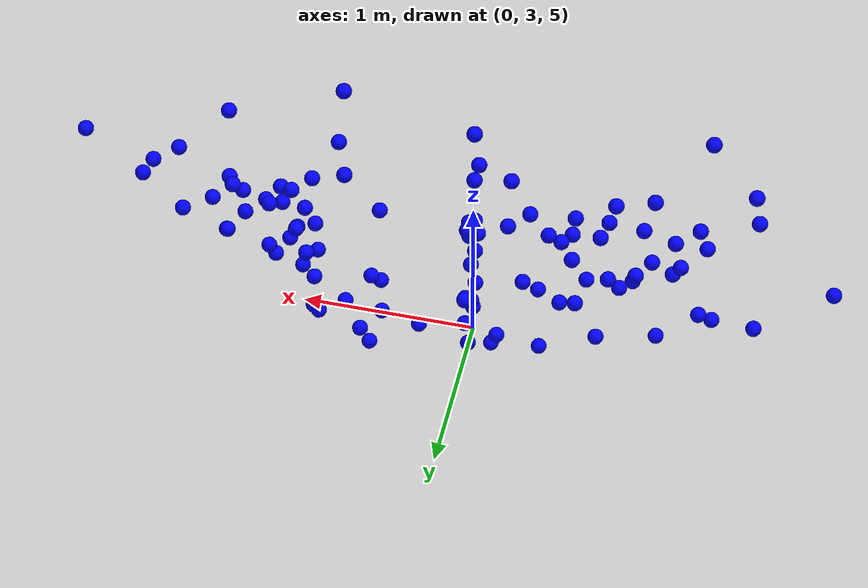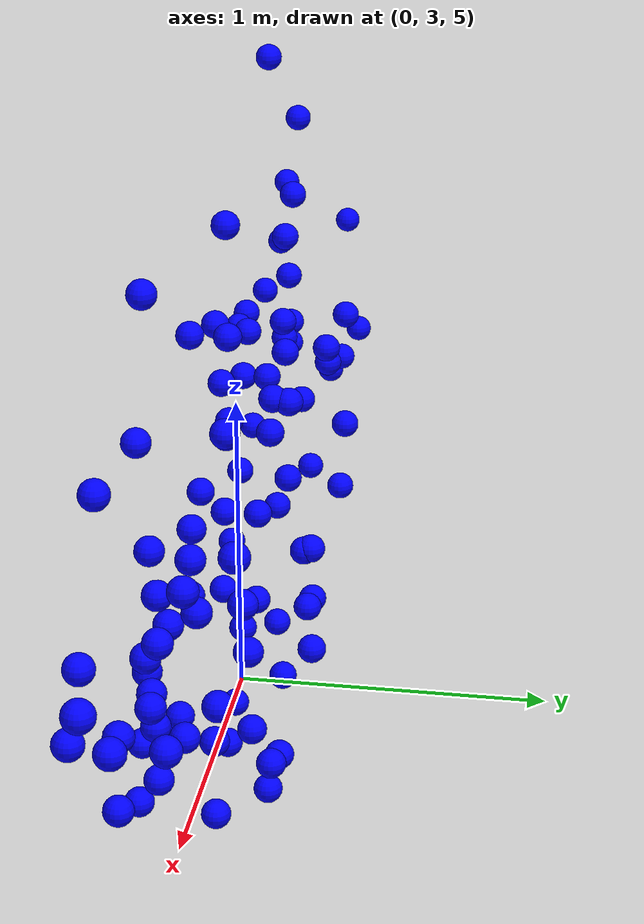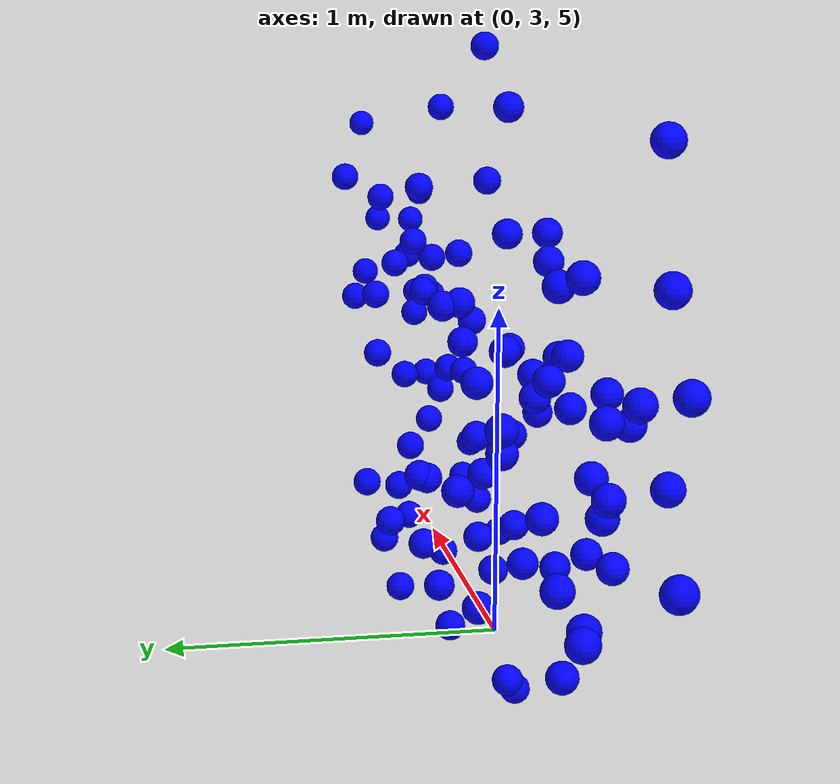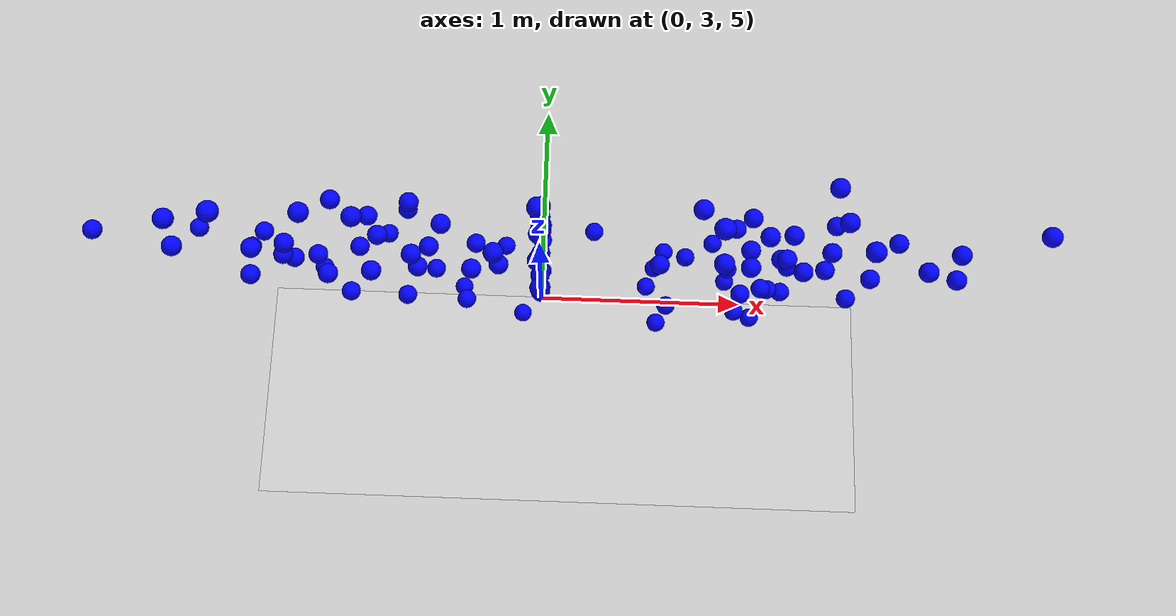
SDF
<sdf version="1.10">
 <world name="sphere">
  <scene>
   <ambient>1 1 1 1</ambient>
   <background>0.800000012 0.800000012 0.800000012 1</background>
   <shadows>true</shadows>
  </scene>
  <gravity>0 0 -9.8000000000000007</gravity>
  <magnetic_field>5.5644999999999998e-06 2.2875799999999999e-05 -4.2388400000000002e-05</magnetic_field>
  <atmosphere type="adiabatic"/>
  <physics type="ode">
   <max_step_size>0.001</max_step_size>
   <real_time_factor>1</real_time_factor>
   <real_time_update_rate>1000</real_time_update_rate>
  </physics>
  <model name="ground_plane">
   <static>true</static>
   <link name="link">
    <collision name="collision">
     <geometry><plane><normal>0 0 1</normal><size>100 100</size></plane></geometry>
    </collision>
    <visual name="visual">
     <geometry><plane><normal>0 0 1</normal><size>100 100</size></plane></geometry>
     <material>
      <ambient>0.800000012 0.800000012 0.800000012 1</ambient>
      <diffuse>0.800000012 0.800000012 0.800000012 1</diffuse>
      <specular>0.800000012 0.800000012 0.800000012 1</specular>
     </material>
    </visual>
    <inertial>
     <mass>1</mass>
     <inertia><ixx>1</ixx><ixy>0</ixy><ixz>0</ixz><iyy>1</iyy><iyz>0</iyz><izz>1</izz></inertia>
    </inertial>
   </link>
  </model>
  <model name="sphere_00">
   <pose>-0.8101000189781189 3.01882004737854 6.2474203109741211 0 0 0</pose>
   <link name="sphere_link">
    <inertial>
     <inertia>
      <ixx>0.10000000000000001</ixx>
      <ixy>0</ixy>
      <ixz>0</ixz>
      <iyy>0.10000000000000001</iyy>
      <iyz>0</iyz>
      <izz>0.10000000000000001</izz>
     </inertia>
     <mass>1</mass>
    </inertial>
    <collision name="sphere_collision">
     <geometry><sphere><radius>0.044999999999999998</radius></sphere></geometry>
    </collision>
    <visual name="sphere_visual">
     <geometry><sphere><radius>0.044999999999999998</radius></sphere></geometry>
     <material><ambient>0 0 1 1</ambient><diffuse>0 0 1 1</diffuse><specular>0 0 1 1</specular></material>
    </visual>
   </link>
   <static>false</static>
   <self_collide>true</self_collide>
  </model>
  <model name="sphere_01">
   <pose>-0.30862641334533691 3.1076400279998779 5.5938301086425781 0 0 0</pose>
   <link name="sphere_link">
    <inertial>
     <inertia>
      <ixx>0.10000000000000001</ixx>
      <ixy>0</ixy>
      <ixz>0</ixz>
      <iyy>0.10000000000000001</iyy>
      <iyz>0</iyz>
      <izz>0.10000000000000001</izz>
     </inertia>
     <mass>1</mass>
    </inertial>
    <collision name="sphere_collision">
     <geometry><sphere><radius>0.044999999999999998</radius></sphere></geometry>
    </collision>
    <visual name="sphere_visual">
     <geometry><sphere><radius>0.044999999999999998</radius></sphere></geometry>
     <material><ambient>0 0 1 1</ambient><diffuse>0 0 1 1</diffuse><specular>0 0 1 1</specular></material>
    </visual>
   </link>
   <static>false</static>
   <self_collide>true</self_collide>
  </model>
  <model name="sphere_02">
   <pose>-0.18142400681972504 3.2076399326324463 5.2198047637939453 0 0 0</pose>
   <link name="sphere_link">
    <inertial>
     <inertia>
      <ixx>0.10000000000000001</ixx>
      <ixy>0</ixy>
      <ixz>0</ixz>
      <iyy>0.10000000000000001</iyy>
      <iyz>0</iyz>
      <izz>0.10000000000000001</izz>
     </inertia>
     <mass>1</mass>
    </inertial>
    <collision name="sphere_collision">
     <geometry><sphere><radius>0.044999999999999998</radius></sphere></geometry>
    </collision>
    <visual name="sphere_visual">
     <geometry><sphere><radius>0.044999999999999998</radius></sphere></geometry>
     <material><ambient>0 0 1 1</ambient><diffuse>0 0 1 1</diffuse><specular>0 0 1 1</specular></material>
    </visual>
   </link>
   <static>false</static>
   <self_collide>true</self_collide>
  </model>
  <model name="sphere_03">
   <pose>1.3758639097213745 3.2076399326324463 5.7371301651000977 0 0 0</pose>
   <link name="sphere_link">
    <inertial>
     <inertia>
      <ixx>0.10000000000000001</ixx>
      <ixy>0</ixy>
      <ixz>0</ixz>
      <iyy>0.10000000000000001</iyy>
      <iyz>0</iyz>
      <izz>0.10000000000000001</izz>
     </inertia>
     <mass>1</mass>
    </inertial>
    <collision name="sphere_collision">
     <geometry><sphere><radius>0.044999999999999998</radius></sphere></geometry>
    </collision>
    <visual name="sphere_visual">
     <geometry><sphere><radius>0.044999999999999998</radius></sphere></geometry>
     <material><ambient>0 0 1 1</ambient><diffuse>0 0 1 1</diffuse><specular>0 0 1 1</specular></material>
    </visual>
   </link>
   <static>false</static>
   <self_collide>true</self_collide>
  </model>
  <model name="sphere_04">
   <pose>0.90909630060195923 3.0961899757385254 5.3272900581359863 0 0 0</pose>
   <link name="sphere_link">
    <inertial>
     <inertia>
      <ixx>0.10000000000000001</ixx>
      <ixy>0</ixy>
      <ixz>0</ixz>
      <iyy>0.10000000000000001</iyy>
      <iyz>0</iyz>
      <izz>0.10000000000000001</izz>
     </inertia>
     <mass>1</mass>
    </inertial>
    <collision name="sphere_collision">
     <geometry><sphere><radius>0.044999999999999998</radius></sphere></geometry>
    </collision>
    <visual name="sphere_visual">
     <geometry><sphere><radius>0.044999999999999998</radius></sphere></geometry>
     <material><ambient>0 0 1 1</ambient><diffuse>0 0 1 1</diffuse><specular>0 0 1 1</specular></material>
    </visual>
   </link>
   <static>false</static>
   <self_collide>true</self_collide>
  </model>
  <model name="sphere_05">
   <pose>0 2.9661004543304443 5.8801798820495605 0 0 0</pose>
   <link name="sphere_link">
    <inertial>
     <inertia>
      <ixx>0.10000000000000001</ixx>
      <ixy>0</ixy>
      <ixz>0</ixz>
      <iyy>0.10000000000000001</iyy>
      <iyz>0</iyz>
      <izz>0.10000000000000001</izz>
     </inertia>
     <mass>1</mass>
    </inertial>
    <collision name="sphere_collision">
     <geometry><sphere><radius>0.044999999999999998</radius></sphere></geometry>
    </collision>
    <visual name="sphere_visual">
     <geometry><sphere><radius>0.044999999999999998</radius></sphere></geometry>
     <material><ambient>0 0 1 1</ambient><diffuse>0 0 1 1</diffuse><specular>0 0 1 1</specular></material>
    </visual>
   </link>
   <static>false</static>
   <self_collide>true</self_collide>
  </model>
  <model name="sphere_06">
   <pose>0.52478998899459839 3.0577552318572998 5.0836100578308105 0 0 0</pose>
   <link name="sphere_link">
    <inertial>
     <inertia>
      <ixx>0.10000000000000001</ixx>
      <ixy>0</ixy>
      <ixz>0</ixz>
      <iyy>0.10000000000000001</iyy>
      <iyz>0</iyz>
      <izz>0.10000000000000001</izz>
     </inertia>
     <mass>1</mass>
     <pose>0 0 0.69999999999999996 0 0 0</pose>
    </inertial>
    <collision name="sphere_collision">
     <geometry><sphere><radius>0.044999999999999998</radius></sphere></geometry>
    </collision>
    <visual name="sphere_visual">
     <geometry><sphere><radius>0.044999999999999998</radius></sphere></geometry>
     <material><ambient>0 0 1 1</ambient><diffuse>0 0 1 1</diffuse><specular>0 0 1 1</specular></material>
    </visual>
   </link>
   <static>false</static>
   <self_collide>true</self_collide>
  </model>
  <model name="sphere_07">
   <pose>0.84674102067947388 3.2525029182434082 5.2275600433349609 0 0 0</pose>
   <link name="sphere_link">
    <inertial>
     <inertia>
      <ixx>0.10000000000000001</ixx>
      <ixy>0</ixy>
      <ixz>0</ixz>
      <iyy>0.10000000000000001</iyy>
      <iyz>0</iyz>
      <izz>0.10000000000000001</izz>
     </inertia>
     <mass>1</mass>
    </inertial>
    <collision name="sphere_collision">
     <geometry><sphere><radius>0.044999999999999998</radius></sphere></geometry>
    </collision>
    <visual name="sphere_visual">
     <geometry><sphere><radius>0.044999999999999998</radius></sphere></geometry>
     <material><ambient>0 0 1 1</ambient><diffuse>0 0 1 1</diffuse><specular>0 0 1 1</specular></material>
    </visual>
   </link>
   <static>false</static>
   <self_collide>true</self_collide>
  </model>
  <model name="sphere_08">
   <pose>0 3.0543978214263916 5.3013801574707031 0 0 0</pose>
   <link name="sphere_link">
    <inertial>
     <inertia>
      <ixx>0.10000000000000001</ixx>
      <ixy>0</ixy>
      <ixz>0</ixz>
      <iyy>0.10000000000000001</iyy>
      <iyz>0</iyz>
      <izz>0.10000000000000001</izz>
     </inertia>
     <mass>1</mass>
    </inertial>
    <collision name="sphere_collision">
     <geometry><sphere><radius>0.044999999999999998</radius></sphere></geometry>
    </collision>
    <visual name="sphere_visual">
     <geometry><sphere><radius>0.044999999999999998</radius></sphere></geometry>
     <material><ambient>0 0 1 1</ambient><diffuse>0 0 1 1</diffuse><specular>0 0 1 1</specular></material>
    </visual>
   </link>
   <static>false</static>
   <self_collide>true</self_collide>
  </model>
  <model name="sphere_09">
   <pose>-0.50494199991226196 3.0061700344085693 5.8660669326782227 0 0 0</pose>
   <link name="sphere_link">
    <inertial>
     <inertia>
      <ixx>0.10000000000000001</ixx>
      <ixy>0</ixy>
      <ixz>0</ixz>
      <iyy>0.10000000000000001</iyy>
      <iyz>0</iyz>
      <izz>0.10000000000000001</izz>
     </inertia>
     <mass>1</mass>
     <pose>0 0 0.69999999999999996 0 0 0</pose>
    </inertial>
    <collision name="sphere_collision">
     <geometry><sphere><radius>0.044999999999999998</radius></sphere></geometry>
    </collision>
    <visual name="sphere_visual">
     <geometry><sphere><radius>0.044999999999999998</radius></sphere></geometry>
     <material><ambient>0 0 1 1</ambient><diffuse>0 0 1 1</diffuse><specular>0 0 1 1</specular></material>
    </visual>
   </link>
   <static>false</static>
   <self_collide>true</self_collide>
  </model>
  <model name="sphere_10">
   <pose>0 3.2213499546051025 5.2891402244567871 0 0 0</pose>
   <link name="sphere_link">
    <inertial>
     <inertia>
      <ixx>0.10000000000000001</ixx>
      <ixy>0</ixy>
      <ixz>0</ixz>
      <iyy>0.10000000000000001</iyy>
      <iyz>0</iyz>
      <izz>0.10000000000000001</izz>
     </inertia>
     <mass>1</mass>
     <pose>0 0 0.69999999999999996 0 0 0</pose>
    </inertial>
    <collision name="sphere_collision">
     <geometry><sphere><radius>0.044999999999999998</radius></sphere></geometry>
    </collision>
    <visual name="sphere_visual">
     <geometry><sphere><radius>0.044999999999999998</radius></sphere></geometry>
     <material><ambient>0 0 1 1</ambient><diffuse>0 0 1 1</diffuse><specular>0 0 1 1</specular></material>
    </visual>
   </link>
   <static>false</static>
   <self_collide>true</self_collide>
  </model>
  <model name="sphere_11">
   <pose>0 2.9791254997253418 6.5953397750854492 0 0 0</pose>
   <link name="sphere_link">
    <inertial>
     <inertia>
      <ixx>0.10000000000000001</ixx>
      <ixy>0</ixy>
      <ixz>0</ixz>
      <iyy>0.10000000000000001</iyy>
      <iyz>0</iyz>
      <izz>0.10000000000000001</izz>
     </inertia>
     <mass>1</mass>
     <pose>0 0 0.69999999999999996 0 0 0</pose>
    </inertial>
    <collision name="sphere_collision">
     <geometry><sphere><radius>0.044999999999999998</radius></sphere></geometry>
    </collision>
    <visual name="sphere_visual">
     <geometry><sphere><radius>0.044999999999999998</radius></sphere></geometry>
     <material><ambient>0 0 1 1</ambient><diffuse>0 0 1 1</diffuse><specular>0 0 1 1</specular></material>
    </visual>
   </link>
   <static>false</static>
   <self_collide>true</self_collide>
  </model>
  <model name="sphere_12">
   <pose>1.1540199518203735 3.1078150272369385 5.8965902328491211 0 0 0</pose>
   <link name="sphere_link">
    <inertial>
     <inertia>
      <ixx>0.10000000000000001</ixx>
      <ixy>0</ixy>
      <ixz>0</ixz>
      <iyy>0.10000000000000001</iyy>
      <iyz>0</iyz>
      <izz>0.10000000000000001</izz>
     </inertia>
     <mass>1</mass>
     <pose>0 0 0.69999999999999996 0 0 0</pose>
    </inertial>
    <collision name="sphere_collision">
     <geometry><sphere><radius>0.044999999999999998</radius></sphere></geometry>
    </collision>
    <visual name="sphere_visual">
     <geometry><sphere><radius>0.044999999999999998</radius></sphere></geometry>
     <material><ambient>0 0 1 1</ambient><diffuse>0 0 1 1</diffuse><specular>0 0 1 1</specular></material>
    </visual>
   </link>
   <static>false</static>
   <self_collide>true</self_collide>
  </model>
  <model name="sphere_13">
   <pose>0.25382706522941589 3.2772500514984131 5.2821002006530762 0 0 0</pose>
   <link name="sphere_link">
    <inertial>
     <inertia>
      <ixx>0.10000000000000001</ixx>
      <ixy>0</ixy>
      <ixz>0</ixz>
      <iyy>0.10000000000000001</iyy>
      <iyz>0</iyz>
      <izz>0.10000000000000001</izz>
     </inertia>
     <mass>1</mass>
     <pose>0 0 0.69999999999999996 0 0 0</pose>
    </inertial>
    <collision name="sphere_collision">
     <geometry><sphere><radius>0.044999999999999998</radius></sphere></geometry>
    </collision>
    <visual name="sphere_visual">
     <geometry><sphere><radius>0.044999999999999998</radius></sphere></geometry>
     <material><ambient>0 0 1 1</ambient><diffuse>0 0 1 1</diffuse><specular>0 0 1 1</specular></material>
    </visual>
   </link>
   <static>false</static>
   <self_collide>true</self_collide>
  </model>
  <model name="sphere_14">
   <pose>1.0408979654312134 2.9444799423217773 5.5553398132324219 0 0 0</pose>
   <link name="sphere_link">
    <inertial>
     <inertia>
      <ixx>0.10000000000000001</ixx>
      <ixy>0</ixy>
      <ixz>0</ixz>
      <iyy>0.10000000000000001</iyy>
      <iyz>0</iyz>
      <izz>0.10000000000000001</izz>
     </inertia>
     <mass>1</mass>
     <pose>0 0 0.69999999999999996 0 0 0</pose>
    </inertial>
    <collision name="sphere_collision">
     <geometry><sphere><radius>0.044999999999999998</radius></sphere></geometry>
    </collision>
    <visual name="sphere_visual">
     <geometry><sphere><radius>0.044999999999999998</radius></sphere></geometry>
     <material><ambient>0 0 1 1</ambient><diffuse>0 0 1 1</diffuse><specular>0 0 1 1</specular></material>
    </visual>
   </link>
   <static>false</static>
   <self_collide>true</self_collide>
  </model>
  <model name="sphere_15">
   <pose>-0.19403360784053802 2.8993599414825439 6.1798100471496582 0 0 0</pose>
   <link name="sphere_link">
    <inertial>
     <inertia>
      <ixx>0.10000000000000001</ixx>
      <ixy>0</ixy>
      <ixz>0</ixz>
      <iyy>0.10000000000000001</iyy>
      <iyz>0</iyz>
      <izz>0.10000000000000001</izz>
     </inertia>
     <mass>1</mass>
     <pose>0 0 0.69999999999999996 0 0 0</pose>
    </inertial>
    <collision name="sphere_collision">
     <geometry><sphere><radius>0.044999999999999998</radius></sphere></geometry>
    </collision>
    <visual name="sphere_visual">
     <geometry><sphere><radius>0.044999999999999998</radius></sphere></geometry>
     <material><ambient>0 0 1 1</ambient><diffuse>0 0 1 1</diffuse><specular>0 0 1 1</specular></material>
    </visual>
   </link>
   <static>false</static>
   <self_collide>true</self_collide>
  </model>
  <model name="sphere_16">
   <pose>-1.3119100332260132 2.8792433738708496 6.7110099792480469 0 0 0</pose>
   <link name="sphere_link">
    <inertial>
     <inertia>
      <ixx>0.10000000000000001</ixx>
      <ixy>0</ixy>
      <ixz>0</ixz>
      <iyy>0.10000000000000001</iyy>
      <iyz>0</iyz>
      <izz>0.10000000000000001</izz>
     </inertia>
     <mass>1</mass>
     <pose>0 0 0.69999999999999996 0 0 0</pose>
    </inertial>
    <collision name="sphere_collision">
     <geometry><sphere><radius>0.044999999999999998</radius></sphere></geometry>
    </collision>
    <visual name="sphere_visual">
     <geometry><sphere><radius>0.044999999999999998</radius></sphere></geometry>
     <material><ambient>0 0 1 1</ambient><diffuse>0 0 1 1</diffuse><specular>0 0 1 1</specular></material>
    </visual>
   </link>
   <static>false</static>
   <self_collide>true</self_collide>
  </model>
  <model name="sphere_17">
   <pose>1.1766971349716187 3.0682199001312256 5.5024600028991699 0 0 0</pose>
   <link name="sphere_link">
    <inertial>
     <inertia>
      <ixx>0.10000000000000001</ixx>
      <ixy>0</ixy>
      <ixz>0</ixz>
      <iyy>0.10000000000000001</iyy>
      <iyz>0</iyz>
      <izz>0.10000000000000001</izz>
     </inertia>
     <mass>1</mass>
     <pose>0 0 0.69999999999999996 0 0 0</pose>
    </inertial>
    <collision name="sphere_collision">
     <geometry><sphere><radius>0.044999999999999998</radius></sphere></geometry>
    </collision>
    <visual name="sphere_visual">
     <geometry><sphere><radius>0.044999999999999998</radius></sphere></geometry>
     <material><ambient>0 0 1 1</ambient><diffuse>0 0 1 1</diffuse><specular>0 0 1 1</specular></material>
    </visual>
   </link>
   <static>false</static>
   <self_collide>true</self_collide>
  </model>
  <model name="sphere_18">
   <pose>1.3726999759674072 3.1196067333221436 6.0826001167297363 0 0 0</pose>
   <link name="sphere_link">
    <inertial>
     <inertia>
      <ixx>0.10000000000000001</ixx>
      <ixy>0</ixy>
      <ixz>0</ixz>
      <iyy>0.10000000000000001</iyy>
      <iyz>0</iyz>
      <izz>0.10000000000000001</izz>
     </inertia>
     <mass>1</mass>
     <pose>0 0 0.69999999999999996 0 0 0</pose>
    </inertial>
    <collision name="sphere_collision">
     <geometry><sphere><radius>0.044999999999999998</radius></sphere></geometry>
    </collision>
    <visual name="sphere_visual">
     <geometry><sphere><radius>0.044999999999999998</radius></sphere></geometry>
     <material><ambient>0 0 1 1</ambient><diffuse>0 0 1 1</diffuse><specular>0 0 1 1</specular></material>
    </visual>
   </link>
   <static>false</static>
   <self_collide>true</self_collide>
  </model>
  <model name="sphere_19">
   <pose>-0.74941295385360718 2.8662300109863281 5.9346098899841309 0 0 0</pose>
   <link name="sphere_link">
    <inertial>
     <inertia>
      <ixx>0.10000000000000001</ixx>
      <ixy>0</ixy>
      <ixz>0</ixz>
      <iyy>0.10000000000000001</iyy>
      <iyz>0</iyz>
      <izz>0.10000000000000001</izz>
     </inertia>
     <mass>1</mass>
     <pose>0 0 0.69999999999999996 0 0 0</pose>
    </inertial>
    <collision name="sphere_collision">
     <geometry><sphere><radius>0.044999999999999998</radius></sphere></geometry>
    </collision>
    <visual name="sphere_visual">
     <geometry><sphere><radius>0.044999999999999998</radius></sphere></geometry>
     <material><ambient>0 0 1 1</ambient><diffuse>0 0 1 1</diffuse><specular>0 0 1 1</specular></material>
    </visual>
   </link>
   <static>false</static>
   <self_collide>true</self_collide>
  </model>
  <model name="sphere_20">
   <pose>1.5283499956130981 2.966209888458252 5.7112307548522949 0 0 0</pose>
   <link name="sphere_link">
    <inertial>
     <inertia>
      <ixx>0.10000000000000001</ixx>
      <ixy>0</ixy>
      <ixz>0</ixz>
      <iyy>0.10000000000000001</iyy>
      <iyz>0</iyz>
      <izz>0.10000000000000001</izz>
     </inertia>
     <mass>1</mass>
     <pose>0 0 0.69999999999999996 0 0 0</pose>
    </inertial>
    <collision name="sphere_collision">
     <geometry><sphere><radius>0.044999999999999998</radius></sphere></geometry>
    </collision>
    <visual name="sphere_visual">
     <geometry><sphere><radius>0.044999999999999998</radius></sphere></geometry>
     <material><ambient>0 0 1 1</ambient><diffuse>0 0 1 1</diffuse><specular>0 0 1 1</specular></material>
    </visual>
   </link>
   <static>false</static>
   <self_collide>true</self_collide>
  </model>
  <model name="sphere_21">
   <pose>2.2217400074005127 3.0480799674987793 6.2031421661376953 0 0 0</pose>
   <link name="sphere_link">
    <inertial>
     <inertia>
      <ixx>0.10000000000000001</ixx>
      <ixy>0</ixy>
      <ixz>0</ixz>
      <iyy>0.10000000000000001</iyy>
      <iyz>0</iyz>
      <izz>0.10000000000000001</izz>
     </inertia>
     <mass>1</mass>
     <pose>0 0 0.69999999999999996 0 0 0</pose>
    </inertial>
    <collision name="sphere_collision">
     <geometry><sphere><radius>0.044999999999999998</radius></sphere></geometry>
    </collision>
    <visual name="sphere_visual">
     <geometry><sphere><radius>0.044999999999999998</radius></sphere></geometry>
     <material><ambient>0 0 1 1</ambient><diffuse>0 0 1 1</diffuse><specular>0 0 1 1</specular></material>
    </visual>
   </link>
   <static>false</static>
   <self_collide>true</self_collide>
  </model>
  <model name="sphere_22">
   <pose>-1.0258899927139282 3.0086886882781982 6.3174500465393066 0 0 0</pose>
   <link name="sphere_link">
    <inertial>
     <inertia>
      <ixx>0.10000000000000001</ixx>
      <ixy>0</ixy>
      <ixz>0</ixz>
      <iyy>0.10000000000000001</iyy>
      <iyz>0</iyz>
      <izz>0.10000000000000001</izz>
     </inertia>
     <mass>1</mass>
     <pose>0 0 0.69999999999999996 0 0 0</pose>
    </inertial>
    <collision name="sphere_collision">
     <geometry><sphere><radius>0.044999999999999998</radius></sphere></geometry>
    </collision>
    <visual name="sphere_visual">
     <geometry><sphere><radius>0.044999999999999998</radius></sphere></geometry>
     <material><ambient>0 0 1 1</ambient><diffuse>0 0 1 1</diffuse><specular>0 0 1 1</specular></material>
    </visual>
   </link>
   <static>false</static>
   <self_collide>true</self_collide>
  </model>
  <model name="sphere_23">
   <pose>1.7234451770782471 2.9191300868988037 6.0306200981140137 0 0 0</pose>
   <link name="sphere_link">
    <inertial>
     <inertia>
      <ixx>0.10000000000000001</ixx>
      <ixy>0</ixy>
      <ixz>0</ixz>
      <iyy>0.10000000000000001</iyy>
      <iyz>0</iyz>
      <izz>0.10000000000000001</izz>
     </inertia>
     <mass>1</mass>
     <pose>0 0 0.69999999999999996 0 0 0</pose>
    </inertial>
    <collision name="sphere_collision">
     <geometry><sphere><radius>0.044999999999999998</radius></sphere></geometry>
    </collision>
    <visual name="sphere_visual">
     <geometry><sphere><radius>0.044999999999999998</radius></sphere></geometry>
     <material><ambient>0 0 1 1</ambient><diffuse>0 0 1 1</diffuse><specular>0 0 1 1</specular></material>
    </visual>
   </link>
   <static>false</static>
   <self_collide>true</self_collide>
  </model>
  <model name="sphere_24">
   <pose>0.920390784740448 3.0976099967956543 5.0828800201416016 0 0 0</pose>
   <link name="sphere_link">
    <inertial>
     <inertia>
      <ixx>0.10000000000000001</ixx>
      <ixy>0</ixy>
      <ixz>0</ixz>
      <iyy>0.10000000000000001</iyy>
      <iyz>0</iyz>
      <izz>0.10000000000000001</izz>
     </inertia>
     <mass>1</mass>
     <pose>0 0 0.69999999999999996 0 0 0</pose>
    </inertial>
    <collision name="sphere_collision">
     <geometry><sphere><radius>0.044999999999999998</radius></sphere></geometry>
    </collision>
    <visual name="sphere_visual">
     <geometry><sphere><radius>0.044999999999999998</radius></sphere></geometry>
     <material><ambient>0 0 1 1</ambient><diffuse>0 0 1 1</diffuse><specular>0 0 1 1</specular></material>
    </visual>
   </link>
   <static>false</static>
   <self_collide>true</self_collide>
  </model>
  <model name="sphere_25">
   <pose>1.1628700494766235 2.9856400489807129 5.3452863693237305 0 0 0</pose>
   <link name="sphere_link">
    <inertial>
     <inertia>
      <ixx>0.10000000000000001</ixx>
      <ixy>0</ixy>
      <ixz>0</ixz>
      <iyy>0.10000000000000001</iyy>
      <iyz>0</iyz>
      <izz>0.10000000000000001</izz>
     </inertia>
     <mass>1</mass>
     <pose>0 0 0.69999999999999996 0 0 0</pose>
    </inertial>
    <collision name="sphere_collision">
     <geometry><sphere><radius>0.044999999999999998</radius></sphere></geometry>
    </collision>
    <visual name="sphere_visual">
     <geometry><sphere><radius>0.044999999999999998</radius></sphere></geometry>
     <material><ambient>0 0 1 1</ambient><diffuse>0 0 1 1</diffuse><specular>0 0 1 1</specular></material>
    </visual>
   </link>
   <static>false</static>
   <self_collide>true</self_collide>
  </model>
  <model name="sphere_26">
   <pose>0 2.8582220077514648 6.2225799560546875 0 0 0</pose>
   <link name="sphere_link">
    <inertial>
     <inertia>
      <ixx>0.10000000000000001</ixx>
      <ixy>0</ixy>
      <ixz>0</ixz>
      <iyy>0.10000000000000001</iyy>
      <iyz>0</iyz>
      <izz>0.10000000000000001</izz>
     </inertia>
     <mass>1</mass>
     <pose>0 0 0.69999999999999996 0 0 0</pose>
    </inertial>
    <collision name="sphere_collision">
     <geometry><sphere><radius>0.044999999999999998</radius></sphere></geometry>
    </collision>
    <visual name="sphere_visual">
     <geometry><sphere><radius>0.044999999999999998</radius></sphere></geometry>
     <material><ambient>0 0 1 1</ambient><diffuse>0 0 1 1</diffuse><specular>0 0 1 1</specular></material>
    </visual>
   </link>
   <static>false</static>
   <self_collide>true</self_collide>
  </model>
  <model name="sphere_27">
   <pose>1.4216636419296265 2.9017300605773926 6.3804302215576172 0 0 0</pose>
   <link name="sphere_link">
    <inertial>
     <inertia>
      <ixx>0.10000000000000001</ixx>
      <ixy>0</ixy>
      <ixz>0</ixz>
      <iyy>0.10000000000000001</iyy>
      <iyz>0</iyz>
      <izz>0.10000000000000001</izz>
     </inertia>
     <mass>1</mass>
     <pose>0 0 0.69999999999999996 0 0 0</pose>
    </inertial>
    <collision name="sphere_collision">
     <geometry><sphere><radius>0.044999999999999998</radius></sphere></geometry>
    </collision>
    <visual name="sphere_visual">
     <geometry><sphere><radius>0.044999999999999998</radius></sphere></geometry>
     <material><ambient>0 0 1 1</ambient><diffuse>0 0 1 1</diffuse><specular>0 0 1 1</specular></material>
    </visual>
   </link>
   <static>false</static>
   <self_collide>true</self_collide>
  </model>
  <model name="sphere_28">
   <pose>1.6581699848175049 3.1258094310760498 5.7612099647521973 0 0 0</pose>
   <link name="sphere_link">
    <inertial>
     <inertia>
      <ixx>0.10000000000000001</ixx>
      <ixy>0</ixy>
      <ixz>0</ixz>
      <iyy>0.10000000000000001</iyy>
      <iyz>0</iyz>
      <izz>0.10000000000000001</izz>
     </inertia>
     <mass>1</mass>
     <pose>0 0 0.69999999999999996 0 0 0</pose>
    </inertial>
    <collision name="sphere_collision">
     <geometry><sphere><radius>0.044999999999999998</radius></sphere></geometry>
    </collision>
    <visual name="sphere_visual">
     <geometry><sphere><radius>0.044999999999999998</radius></sphere></geometry>
     <material><ambient>0 0 1 1</ambient><diffuse>0 0 1 1</diffuse><specular>0 0 1 1</specular></material>
    </visual>
   </link>
   <static>false</static>
   <self_collide>true</self_collide>
  </model>
  <model name="sphere_29">
   <pose>0 2.9778904914855957 6.2235097885131836 0 0 0</pose>
   <link name="sphere_link">
    <inertial>
     <inertia>
      <ixx>0.10000000000000001</ixx>
      <ixy>0</ixy>
      <ixz>0</ixz>
      <iyy>0.10000000000000001</iyy>
      <iyz>0</iyz>
      <izz>0.10000000000000001</izz>
     </inertia>
     <mass>1</mass>
     <pose>0 0 0.69999999999999996 0 0 0</pose>
    </inertial>
    <collision name="sphere_collision">
     <geometry><sphere><radius>0.044999999999999998</radius></sphere></geometry>
    </collision>
    <visual name="sphere_visual">
     <geometry><sphere><radius>0.044999999999999998</radius></sphere></geometry>
     <material><ambient>0 0 1 1</ambient><diffuse>0 0 1 1</diffuse><specular>0 0 1 1</specular></material>
    </visual>
   </link>
   <static>false</static>
   <self_collide>true</self_collide>
  </model>
  <model name="sphere_30">
   <pose>0 3.0074362754821777 5.1943202018737793 0 0 0</pose>
   <link name="sphere_link">
    <inertial>
     <inertia>
      <ixx>0.10000000000000001</ixx>
      <ixy>0</ixy>
      <ixz>0</ixz>
      <iyy>0.10000000000000001</iyy>
      <iyz>0</iyz>
      <izz>0.10000000000000001</izz>
     </inertia>
     <mass>1</mass>
     <pose>0 0 0.69999999999999996 0 0 0</pose>
    </inertial>
    <collision name="sphere_collision">
     <geometry><sphere><radius>0.044999999999999998</radius></sphere></geometry>
    </collision>
    <visual name="sphere_visual">
     <geometry><sphere><radius>0.044999999999999998</radius></sphere></geometry>
     <material><ambient>0 0 1 1</ambient><diffuse>0 0 1 1</diffuse><specular>0 0 1 1</specular></material>
    </visual>
   </link>
   <static>false</static>
   <self_collide>true</self_collide>
  </model>
  <model name="sphere_31">
   <pose>-0.85268700122833252 3.0630147457122803 5.6283798217773438 0 0 0</pose>
   <link name="sphere_link">
    <inertial>
     <inertia>
      <ixx>0.10000000000000001</ixx>
      <ixy>0</ixy>
      <ixz>0</ixz>
      <iyy>0.10000000000000001</iyy>
      <iyz>0</iyz>
      <izz>0.10000000000000001</izz>
     </inertia>
     <mass>1</mass>
     <pose>0 0 0.69999999999999996 0 0 0</pose>
    </inertial>
    <collision name="sphere_collision">
     <geometry><sphere><radius>0.044999999999999998</radius></sphere></geometry>
    </collision>
    <visual name="sphere_visual">
     <geometry><sphere><radius>0.044999999999999998</radius></sphere></geometry>
     <material><ambient>0 0 1 1</ambient><diffuse>0 0 1 1</diffuse><specular>0 0 1 1</specular></material>
    </visual>
   </link>
   <static>false</static>
   <self_collide>true</self_collide>
  </model>
  <model name="sphere_32">
   <pose>-1.2731363773345947 2.9205100536346436 6.0470099449157715 0 0 0</pose>
   <link name="sphere_link">
    <inertial>
     <inertia>
      <ixx>0.10000000000000001</ixx>
      <ixy>0</ixy>
      <ixz>0</ixz>
      <iyy>0.10000000000000001</iyy>
      <iyz>0</iyz>
      <izz>0.10000000000000001</izz>
     </inertia>
     <mass>1</mass>
     <pose>0 0 0.69999999999999996 0 0 0</pose>
    </inertial>
    <collision name="sphere_collision">
     <geometry><sphere><radius>0.044999999999999998</radius></sphere></geometry>
    </collision>
    <visual name="sphere_visual">
     <geometry><sphere><radius>0.044999999999999998</radius></sphere></geometry>
     <material><ambient>0 0 1 1</ambient><diffuse>0 0 1 1</diffuse><specular>0 0 1 1</specular></material>
    </visual>
   </link>
   <static>false</static>
   <self_collide>true</self_collide>
  </model>
  <model name="sphere_33">
   <pose>-0.60159999132156372 3.1903257369995117 5.940730094909668 0 0 0</pose>
   <link name="sphere_link">
    <inertial>
     <inertia>
      <ixx>0.10000000000000001</ixx>
      <ixy>0</ixy>
      <ixz>0</ixz>
      <iyy>0.10000000000000001</iyy>
      <iyz>0</iyz>
      <izz>0.10000000000000001</izz>
     </inertia>
     <mass>1</mass>
     <pose>0 0 0.69999999999999996 0 0 0</pose>
    </inertial>
    <collision name="sphere_collision">
     <geometry><sphere><radius>0.044999999999999998</radius></sphere></geometry>
    </collision>
    <visual name="sphere_visual">
     <geometry><sphere><radius>0.044999999999999998</radius></sphere></geometry>
     <material><ambient>0 0 1 1</ambient><diffuse>0 0 1 1</diffuse><specular>0 0 1 1</specular></material>
    </visual>
   </link>
   <static>false</static>
   <self_collide>true</self_collide>
  </model>
  <model name="sphere_34">
   <pose>0 2.9557774066925049 5.6145200729370117 0 0 0</pose>
   <link name="sphere_link">
    <inertial>
     <inertia>
      <ixx>0.10000000000000001</ixx>
      <ixy>0</ixy>
      <ixz>0</ixz>
      <iyy>0.10000000000000001</iyy>
      <iyz>0</iyz>
      <izz>0.10000000000000001</izz>
     </inertia>
     <mass>1</mass>
     <pose>0 0 0.69999999999999996 0 0 0</pose>
    </inertial>
    <collision name="sphere_collision">
     <geometry><sphere><radius>0.044999999999999998</radius></sphere></geometry>
    </collision>
    <visual name="sphere_visual">
     <geometry><sphere><radius>0.044999999999999998</radius></sphere></geometry>
     <material><ambient>0 0 1 1</ambient><diffuse>0 0 1 1</diffuse><specular>0 0 1 1</specular></material>
    </visual>
   </link>
   <static>false</static>
   <self_collide>true</self_collide>
  </model>
  <model name="sphere_35">
   <pose>1.9086498022079468 3.0391800403594971 5.9025201797485352 0 0 0</pose>
   <link name="sphere_link">
    <inertial>
     <inertia>
      <ixx>0.10000000000000001</ixx>
      <ixy>0</ixy>
      <ixz>0</ixz>
      <iyy>0.10000000000000001</iyy>
      <iyz>0</iyz>
      <izz>0.10000000000000001</izz>
     </inertia>
     <mass>1</mass>
     <pose>0 0 0.69999999999999996 0 0 0</pose>
    </inertial>
    <collision name="sphere_collision">
     <geometry><sphere><radius>0.044999999999999998</radius></sphere></geometry>
    </collision>
    <visual name="sphere_visual">
     <geometry><sphere><radius>0.044999999999999998</radius></sphere></geometry>
     <material><ambient>0 0 1 1</ambient><diffuse>0 0 1 1</diffuse><specular>0 0 1 1</specular></material>
    </visual>
   </link>
   <static>false</static>
   <self_collide>true</self_collide>
  </model>
  <model name="sphere_36">
   <pose>0 3.137521505355835 5.0250701904296875 0 0 0</pose>
   <link name="sphere_link">
    <inertial>
     <inertia>
      <ixx>0.10000000000000001</ixx>
      <ixy>0</ixy>
      <ixz>0</ixz>
      <iyy>0.10000000000000001</iyy>
      <iyz>0</iyz>
      <izz>0.10000000000000001</izz>
     </inertia>
     <mass>1</mass>
     <pose>0 0 0.69999999999999996 0 0 0</pose>
    </inertial>
    <collision name="sphere_collision">
     <geometry><sphere><radius>0.044999999999999998</radius></sphere></geometry>
    </collision>
    <visual name="sphere_visual">
     <geometry><sphere><radius>0.044999999999999998</radius></sphere></geometry>
     <material><ambient>0 0 1 1</ambient><diffuse>0 0 1 1</diffuse><specular>0 0 1 1</specular></material>
    </visual>
   </link>
   <static>false</static>
   <self_collide>true</self_collide>
  </model>
  <model name="sphere_37">
   <pose>-1.1448651552200317 2.9704298973083496 5.9682598114013672 0 0 0</pose>
   <link name="sphere_link">
    <inertial>
     <inertia>
      <ixx>0.10000000000000001</ixx>
      <ixy>0</ixy>
      <ixz>0</ixz>
      <iyy>0.10000000000000001</iyy>
      <iyz>0</iyz>
      <izz>0.10000000000000001</izz>
     </inertia>
     <mass>1</mass>
     <pose>0 0 0.69999999999999996 0 0 0</pose>
    </inertial>
    <collision name="sphere_collision">
     <geometry><sphere><radius>0.044999999999999998</radius></sphere></geometry>
    </collision>
    <visual name="sphere_visual">
     <geometry><sphere><radius>0.044999999999999998</radius></sphere></geometry>
     <material><ambient>0 0 1 1</ambient><diffuse>0 0 1 1</diffuse><specular>0 0 1 1</specular></material>
    </visual>
   </link>
   <static>false</static>
   <self_collide>true</self_collide>
  </model>
  <model name="sphere_38">
   <pose>0.70926922559738159 3.1699800491333008 5.2538199424743652 0 0 0</pose>
   <link name="sphere_link">
    <inertial>
     <inertia>
      <ixx>0.10000000000000001</ixx>
      <ixy>0</ixy>
      <ixz>0</ixz>
      <iyy>0.10000000000000001</iyy>
      <iyz>0</iyz>
      <izz>0.10000000000000001</izz>
     </inertia>
     <mass>1</mass>
     <pose>0 0 0.69999999999999996 0 0 0</pose>
    </inertial>
    <collision name="sphere_collision">
     <geometry><sphere><radius>0.044999999999999998</radius></sphere></geometry>
    </collision>
    <visual name="sphere_visual">
     <geometry><sphere><radius>0.044999999999999998</radius></sphere></geometry>
     <material><ambient>0 0 1 1</ambient><diffuse>0 0 1 1</diffuse><specular>0 0 1 1</specular></material>
    </visual>
   </link>
   <static>false</static>
   <self_collide>true</self_collide>
  </model>
  <model name="sphere_39">
   <pose>1.3259987831115723 3.0083398818969727 5.6839499473571777 0 0 0</pose>
   <link name="sphere_link">
    <inertial>
     <inertia>
      <ixx>0.10000000000000001</ixx>
      <ixy>0</ixy>
      <ixz>0</ixz>
      <iyy>0.10000000000000001</iyy>
      <iyz>0</iyz>
      <izz>0.10000000000000001</izz>
     </inertia>
     <mass>1</mass>
     <pose>0 0 0.69999999999999996 0 0 0</pose>
    </inertial>
    <collision name="sphere_collision">
     <geometry><sphere><radius>0.044999999999999998</radius></sphere></geometry>
    </collision>
    <visual name="sphere_visual">
     <geometry><sphere><radius>0.044999999999999998</radius></sphere></geometry>
     <material><ambient>0 0 1 1</ambient><diffuse>0 0 1 1</diffuse><specular>0 0 1 1</specular></material>
    </visual>
   </link>
   <static>false</static>
   <self_collide>true</self_collide>
  </model>
  <model name="sphere_40">
   <pose>1.4648668766021729 2.9401900768280029 5.4328398704528809 0 0 0</pose>
   <link name="sphere_link">
    <inertial>
     <inertia>
      <ixx>0.10000000000000001</ixx>
      <ixy>0</ixy>
      <ixz>0</ixz>
      <iyy>0.10000000000000001</iyy>
      <iyz>0</iyz>
      <izz>0.10000000000000001</izz>
     </inertia>
     <mass>1</mass>
     <pose>0 0 0.69999999999999996 0 0 0</pose>
    </inertial>
    <collision name="sphere_collision">
     <geometry><sphere><radius>0.044999999999999998</radius></sphere></geometry>
    </collision>
    <visual name="sphere_visual">
     <geometry><sphere><radius>0.044999999999999998</radius></sphere></geometry>
     <material><ambient>0 0 1 1</ambient><diffuse>0 0 1 1</diffuse><specular>0 0 1 1</specular></material>
    </visual>
   </link>
   <static>false</static>
   <self_collide>true</self_collide>
  </model>
  <model name="sphere_41">
   <pose>0 3.1170649528503418 6.0235199928283691 0 0 0</pose>
   <link name="sphere_link">
    <inertial>
     <inertia>
      <ixx>0.10000000000000001</ixx>
      <ixy>0</ixy>
      <ixz>0</ixz>
      <iyy>0.10000000000000001</iyy>
      <iyz>0</iyz>
      <izz>0.10000000000000001</izz>
     </inertia>
     <mass>1</mass>
     <pose>0 0 0.69999999999999996 0 0 0</pose>
    </inertial>
    <collision name="sphere_collision">
     <geometry><sphere><radius>0.044999999999999998</radius></sphere></geometry>
    </collision>
    <visual name="sphere_visual">
     <geometry><sphere><radius>0.044999999999999998</radius></sphere></geometry>
     <material><ambient>0 0 1 1</ambient><diffuse>0 0 1 1</diffuse><specular>0 0 1 1</specular></material>
    </visual>
   </link>
   <static>false</static>
   <self_collide>true</self_collide>
  </model>
  <model name="sphere_42">
   <pose>0.54871690273284912 2.9668200016021729 5.8345599174499512 0 0 0</pose>
   <link name="sphere_link">
    <inertial>
     <inertia>
      <ixx>0.10000000000000001</ixx>
      <ixy>0</ixy>
      <ixz>0</ixz>
      <iyy>0.10000000000000001</iyy>
      <iyz>0</iyz>
      <izz>0.10000000000000001</izz>
     </inertia>
     <mass>1</mass>
     <pose>0 0 0.69999999999999996 0 0 0</pose>
    </inertial>
    <collision name="sphere_collision">
     <geometry><sphere><radius>0.044999999999999998</radius></sphere></geometry>
    </collision>
    <visual name="sphere_visual">
     <geometry><sphere><radius>0.044999999999999998</radius></sphere></geometry>
     <material><ambient>0 0 1 1</ambient><diffuse>0 0 1 1</diffuse><specular>0 0 1 1</specular></material>
    </visual>
   </link>
   <static>false</static>
   <self_collide>true</self_collide>
  </model>
  <model name="sphere_43">
   <pose>0.9218519926071167 3.2054018974304199 5.6465001106262207 0 0 0</pose>
   <link name="sphere_link">
    <inertial>
     <inertia>
      <ixx>0.10000000000000001</ixx>
      <ixy>0</ixy>
      <ixz>0</ixz>
      <iyy>0.10000000000000001</iyy>
      <iyz>0</iyz>
      <izz>0.10000000000000001</izz>
     </inertia>
     <mass>1</mass>
     <pose>0 0 0.69999999999999996 0 0 0</pose>
    </inertial>
    <collision name="sphere_collision">
     <geometry><sphere><radius>0.044999999999999998</radius></sphere></geometry>
    </collision>
    <visual name="sphere_visual">
     <geometry><sphere><radius>0.044999999999999998</radius></sphere></geometry>
     <material><ambient>0 0 1 1</ambient><diffuse>0 0 1 1</diffuse><specular>0 0 1 1</specular></material>
    </visual>
   </link>
   <static>false</static>
   <self_collide>true</self_collide>
  </model>
  <model name="sphere_44">
   <pose>0.9764549732208252 3.2027599811553955 5.8323245048522949 0 0 0</pose>
   <link name="sphere_link">
    <inertial>
     <inertia>
      <ixx>0.10000000000000001</ixx>
      <ixy>0</ixy>
      <ixz>0</ixz>
      <iyy>0.10000000000000001</iyy>
      <iyz>0</iyz>
      <izz>0.10000000000000001</izz>
     </inertia>
     <mass>1</mass>
     <pose>0 0 0.69999999999999996 0 0 0</pose>
    </inertial>
    <collision name="sphere_collision">
     <geometry><sphere><radius>0.044999999999999998</radius></sphere></geometry>
    </collision>
    <visual name="sphere_visual">
     <geometry><sphere><radius>0.044999999999999998</radius></sphere></geometry>
     <material><ambient>0 0 1 1</ambient><diffuse>0 0 1 1</diffuse><specular>0 0 1 1</specular></material>
    </visual>
   </link>
   <static>false</static>
   <self_collide>true</self_collide>
  </model>
  <model name="sphere_45">
   <pose>0 2.9454939365386963 5.3318800926208496 0 0 0</pose>
   <link name="sphere_link">
    <inertial>
     <inertia>
      <ixx>0.10000000000000001</ixx>
      <ixy>0</ixy>
      <ixz>0</ixz>
      <iyy>0.10000000000000001</iyy>
      <iyz>0</iyz>
      <izz>0.10000000000000001</izz>
     </inertia>
     <mass>1</mass>
     <pose>0 0 0.69999999999999996 0 0 0</pose>
    </inertial>
    <collision name="sphere_collision">
     <geometry><sphere><radius>0.044999999999999998</radius></sphere></geometry>
    </collision>
    <visual name="sphere_visual">
     <geometry><sphere><radius>0.044999999999999998</radius></sphere></geometry>
     <material><ambient>0 0 1 1</ambient><diffuse>0 0 1 1</diffuse><specular>0 0 1 1</specular></material>
    </visual>
   </link>
   <static>false</static>
   <self_collide>true</self_collide>
  </model>
  <model name="sphere_46">
   <pose>-2.0550100803375244 3.0402500629425049 5.8366270065307617 0 0 0</pose>
   <link name="sphere_link">
    <inertial>
     <inertia>
      <ixx>0.10000000000000001</ixx>
      <ixy>0</ixy>
      <ixz>0</ixz>
      <iyy>0.10000000000000001</iyy>
      <iyz>0</iyz>
      <izz>0.10000000000000001</izz>
     </inertia>
     <mass>1</mass>
     <pose>0 0 0.69999999999999996 0 0 0</pose>
    </inertial>
    <collision name="sphere_collision">
     <geometry><sphere><radius>0.044999999999999998</radius></sphere></geometry>
    </collision>
    <visual name="sphere_visual">
     <geometry><sphere><radius>0.044999999999999998</radius></sphere></geometry>
     <material><ambient>0 0 1 1</ambient><diffuse>0 0 1 1</diffuse><specular>0 0 1 1</specular></material>
    </visual>
   </link>
   <static>false</static>
   <self_collide>true</self_collide>
  </model>
  <model name="sphere_47">
   <pose>0.71168500185012817 3.1084346771240234 6.2366299629211426 0 0 0</pose>
   <link name="sphere_link">
    <inertial>
     <inertia>
      <ixx>0.10000000000000001</ixx>
      <ixy>0</ixy>
      <ixz>0</ixz>
      <iyy>0.10000000000000001</iyy>
      <iyz>0</iyz>
      <izz>0.10000000000000001</izz>
     </inertia>
     <mass>1</mass>
     <pose>0 0 0.69999999999999996 0 0 0</pose>
    </inertial>
    <collision name="sphere_collision">
     <geometry><sphere><radius>0.044999999999999998</radius></sphere></geometry>
    </collision>
    <visual name="sphere_visual">
     <geometry><sphere><radius>0.044999999999999998</radius></sphere></geometry>
     <material><ambient>0 0 1 1</ambient><diffuse>0 0 1 1</diffuse><specular>0 0 1 1</specular></material>
    </visual>
   </link>
   <static>false</static>
   <self_collide>true</self_collide>
  </model>
  <model name="sphere_48">
   <pose>0 3.1077263355255127 5.904900074005127 0 0 0</pose>
   <link name="sphere_link">
    <inertial>
     <inertia>
      <ixx>0.10000000000000001</ixx>
      <ixy>0</ixy>
      <ixz>0</ixz>
      <iyy>0.10000000000000001</iyy>
      <iyz>0</iyz>
      <izz>0.10000000000000001</izz>
     </inertia>
     <mass>1</mass>
     <pose>0 0 0.69999999999999996 0 0 0</pose>
    </inertial>
    <collision name="sphere_collision">
     <geometry><sphere><radius>0.044999999999999998</radius></sphere></geometry>
    </collision>
    <visual name="sphere_visual">
     <geometry><sphere><radius>0.044999999999999998</radius></sphere></geometry>
     <material><ambient>0 0 1 1</ambient><diffuse>0 0 1 1</diffuse><specular>0 0 1 1</specular></material>
    </visual>
   </link>
   <static>false</static>
   <self_collide>true</self_collide>
  </model>
  <model name="sphere_49">
   <pose>0.94022500514984131 2.8869268894195557 5.3212299346923828 0 0 0</pose>
   <link name="sphere_link">
    <inertial>
     <inertia>
      <ixx>0.10000000000000001</ixx>
      <ixy>0</ixy>
      <ixz>0</ixz>
      <iyy>0.10000000000000001</iyy>
      <iyz>0</iyz>
      <izz>0.10000000000000001</izz>
     </inertia>
     <mass>1</mass>
     <pose>0 0 0.69999999999999996 0 0 0</pose>
    </inertial>
    <collision name="sphere_collision">
     <geometry><sphere><radius>0.044999999999999998</radius></sphere></geometry>
    </collision>
    <visual name="sphere_visual">
     <geometry><sphere><radius>0.044999999999999998</radius></sphere></geometry>
     <material><ambient>0 0 1 1</ambient><diffuse>0 0 1 1</diffuse><specular>0 0 1 1</specular></material>
    </visual>
   </link>
   <static>false</static>
   <self_collide>true</self_collide>
  </model>
  <model name="sphere_50">
   <pose>0.80174797773361206 2.8684999942779541 6.2338399887084961 0 0 0</pose>
   <link name="sphere_link">
    <inertial>
     <inertia>
      <ixx>0.10000000000000001</ixx>
      <ixy>0</ixy>
      <ixz>0</ixz>
      <iyy>0.10000000000000001</iyy>
      <iyz>0</iyz>
      <izz>0.10000000000000001</izz>
     </inertia>
     <mass>1</mass>
     <pose>0 0 0.69999999999999996 0 0 0</pose>
    </inertial>
    <collision name="sphere_collision">
     <geometry><sphere><radius>0.044999999999999998</radius></sphere></geometry>
    </collision>
    <visual name="sphere_visual">
     <geometry><sphere><radius>0.044999999999999998</radius></sphere></geometry>
     <material><ambient>0 0 1 1</ambient><diffuse>0 0 1 1</diffuse><specular>0 0 1 1</specular></material>
    </visual>
   </link>
   <static>false</static>
   <self_collide>true</self_collide>
  </model>
  <model name="sphere_51">
   <pose>-0.50798201560974121 3.0342063903808594 5.3864998817443848 0 0 0</pose>
   <link name="sphere_link">
    <inertial>
     <inertia>
      <ixx>0.10000000000000001</ixx>
      <ixy>0</ixy>
      <ixz>0</ixz>
      <iyy>0.10000000000000001</iyy>
      <iyz>0</iyz>
      <izz>0.10000000000000001</izz>
     </inertia>
     <mass>1</mass>
     <pose>0 0 0.69999999999999996 0 0 0</pose>
    </inertial>
    <collision name="sphere_collision">
     <geometry><sphere><radius>0.044999999999999998</radius></sphere></geometry>
    </collision>
    <visual name="sphere_visual">
     <geometry><sphere><radius>0.044999999999999998</radius></sphere></geometry>
     <material><ambient>0 0 1 1</ambient><diffuse>0 0 1 1</diffuse><specular>0 0 1 1</specular></material>
    </visual>
   </link>
   <static>false</static>
   <self_collide>true</self_collide>
  </model>
  <model name="sphere_52">
   <pose>1.0817099809646606 2.9623360633850098 5.4718799591064453 0 0 0</pose>
   <link name="sphere_link">
    <inertial>
     <inertia>
      <ixx>0.10000000000000001</ixx>
      <ixy>0</ixy>
      <ixz>0</ixz>
      <iyy>0.10000000000000001</iyy>
      <iyz>0</iyz>
      <izz>0.10000000000000001</izz>
     </inertia>
     <mass>1</mass>
     <pose>0 0 0.69999999999999996 0 0 0</pose>
    </inertial>
    <collision name="sphere_collision">
     <geometry><sphere><radius>0.044999999999999998</radius></sphere></geometry>
    </collision>
    <visual name="sphere_visual">
     <geometry><sphere><radius>0.044999999999999998</radius></sphere></geometry>
     <material><ambient>0 0 1 1</ambient><diffuse>0 0 1 1</diffuse><specular>0 0 1 1</specular></material>
    </visual>
   </link>
   <static>false</static>
   <self_collide>true</self_collide>
  </model>
  <model name="sphere_53">
   <pose>-0.63582098484039307 3.2473959922790527 5.6487398147583008 0 0 0</pose>
   <link name="sphere_link">
    <inertial>
     <inertia>
      <ixx>0.10000000000000001</ixx>
      <ixy>0</ixy>
      <ixz>0</ixz>
      <iyy>0.10000000000000001</iyy>
      <iyz>0</iyz>
      <izz>0.10000000000000001</izz>
     </inertia>
     <mass>1</mass>
     <pose>0 0 0.69999999999999996 0 0 0</pose>
    </inertial>
    <collision name="sphere_collision">
     <geometry><sphere><radius>0.044999999999999998</radius></sphere></geometry>
    </collision>
    <visual name="sphere_visual">
     <geometry><sphere><radius>0.044999999999999998</radius></sphere></geometry>
     <material><ambient>0 0 1 1</ambient><diffuse>0 0 1 1</diffuse><specular>0 0 1 1</specular></material>
    </visual>
   </link>
   <static>false</static>
   <self_collide>true</self_collide>
  </model>
  <model name="sphere_54">
   <pose>-0.72920799255371094 3.0216891765594482 5.9718399047851562 0 0 0</pose>
   <link name="sphere_link">
    <inertial>
     <inertia>
      <ixx>0.10000000000000001</ixx>
      <ixy>0</ixy>
      <ixz>0</ixz>
      <iyy>0.10000000000000001</iyy>
      <iyz>0</iyz>
      <izz>0.10000000000000001</izz>
     </inertia>
     <mass>1</mass>
     <pose>0 0 0.69999999999999996 0 0 0</pose>
    </inertial>
    <collision name="sphere_collision">
     <geometry><sphere><radius>0.044999999999999998</radius></sphere></geometry>
    </collision>
    <visual name="sphere_visual">
     <geometry><sphere><radius>0.044999999999999998</radius></sphere></geometry>
     <material><ambient>0 0 1 1</ambient><diffuse>0 0 1 1</diffuse><specular>0 0 1 1</specular></material>
    </visual>
   </link>
   <static>false</static>
   <self_collide>true</self_collide>
  </model>
  <model name="sphere_55">
   <pose>0 3.168473482131958 6.0153698921203613 0 0 0</pose>
   <link name="sphere_link">
    <inertial>
     <inertia>
      <ixx>0.10000000000000001</ixx>
      <ixy>0</ixy>
      <ixz>0</ixz>
      <iyy>0.10000000000000001</iyy>
      <iyz>0</iyz>
      <izz>0.10000000000000001</izz>
     </inertia>
     <mass>1</mass>
     <pose>0 0 0.69999999999999996 0 0 0</pose>
    </inertial>
    <collision name="sphere_collision">
     <geometry><sphere><radius>0.044999999999999998</radius></sphere></geometry>
    </collision>
    <visual name="sphere_visual">
     <geometry><sphere><radius>0.044999999999999998</radius></sphere></geometry>
     <material><ambient>0 0 1 1</ambient><diffuse>0 0 1 1</diffuse><specular>0 0 1 1</specular></material>
    </visual>
   </link>
   <static>false</static>
   <self_collide>true</self_collide>
  </model>
  <model name="sphere_56">
   <pose>-0.56873500347137451 2.9315109252929688 5.9971199035644531 0 0 0</pose>
   <link name="sphere_link">
    <inertial>
     <inertia>
      <ixx>0.10000000000000001</ixx>
      <ixy>0</ixy>
      <ixz>0</ixz>
      <iyy>0.10000000000000001</iyy>
      <iyz>0</iyz>
      <izz>0.10000000000000001</izz>
     </inertia>
     <mass>1</mass>
     <pose>0 0 0.69999999999999996 0 0 0</pose>
    </inertial>
    <collision name="sphere_collision">
     <geometry><sphere><radius>0.044999999999999998</radius></sphere></geometry>
    </collision>
    <visual name="sphere_visual">
     <geometry><sphere><radius>0.044999999999999998</radius></sphere></geometry>
     <material><ambient>0 0 1 1</ambient><diffuse>0 0 1 1</diffuse><specular>0 0 1 1</specular></material>
    </visual>
   </link>
   <static>false</static>
   <self_collide>true</self_collide>
  </model>
  <model name="sphere_57">
   <pose>-0.097056999802589417 2.9574806690216064 4.8474798202514648 0 0 0</pose>
   <link name="sphere_link">
    <inertial>
     <inertia>
      <ixx>0.10000000000000001</ixx>
      <ixy>0</ixy>
      <ixz>0</ixz>
      <iyy>0.10000000000000001</iyy>
      <iyz>0</iyz>
      <izz>0.10000000000000001</izz>
     </inertia>
     <mass>1</mass>
     <pose>0 0 0.69999999999999996 0 0 0</pose>
    </inertial>
    <collision name="sphere_collision">
     <geometry><sphere><radius>0.044999999999999998</radius></sphere></geometry>
    </collision>
    <visual name="sphere_visual">
     <geometry><sphere><radius>0.044999999999999998</radius></sphere></geometry>
     <material><ambient>0 0 1 1</ambient><diffuse>0 0 1 1</diffuse><specular>0 0 1 1</specular></material>
    </visual>
   </link>
   <static>false</static>
   <self_collide>true</self_collide>
  </model>
  <model name="sphere_58">
   <pose>0.96352899074554443 3.0467255115509033 5.8408999443054199 0 0 0</pose>
   <link name="sphere_link">
    <inertial>
     <inertia>
      <ixx>0.10000000000000001</ixx>
      <ixy>0</ixy>
      <ixz>0</ixz>
      <iyy>0.10000000000000001</iyy>
      <iyz>0</iyz>
      <izz>0.10000000000000001</izz>
     </inertia>
     <mass>1</mass>
     <pose>0 0 0.69999999999999996 0 0 0</pose>
    </inertial>
    <collision name="sphere_collision">
     <geometry><sphere><radius>0.044999999999999998</radius></sphere></geometry>
    </collision>
    <visual name="sphere_visual">
     <geometry><sphere><radius>0.044999999999999998</radius></sphere></geometry>
     <material><ambient>0 0 1 1</ambient><diffuse>0 0 1 1</diffuse><specular>0 0 1 1</specular></material>
    </visual>
   </link>
   <static>false</static>
   <self_collide>true</self_collide>
  </model>
  <model name="sphere_59">
   <pose>0 3.2348027229309082 5.5027198791503906 0 0 0</pose>
   <link name="sphere_link">
    <inertial>
     <inertia>
      <ixx>0.10000000000000001</ixx>
      <ixy>0</ixy>
      <ixz>0</ixz>
      <iyy>0.10000000000000001</iyy>
      <iyz>0</iyz>
      <izz>0.10000000000000001</izz>
     </inertia>
     <mass>1</mass>
     <pose>0 0 0.69999999999999996 0 0 0</pose>
    </inertial>
    <collision name="sphere_collision">
     <geometry><sphere><radius>0.044999999999999998</radius></sphere></geometry>
    </collision>
    <visual name="sphere_visual">
     <geometry><sphere><radius>0.044999999999999998</radius></sphere></geometry>
     <material><ambient>0 0 1 1</ambient><diffuse>0 0 1 1</diffuse><specular>0 0 1 1</specular></material>
    </visual>
   </link>
   <static>false</static>
   <self_collide>true</self_collide>
  </model>
  <model name="sphere_60">
   <pose>-0.55157202482223511 2.9167957305908203 5.8429899215698242 0 0 0</pose>
   <link name="sphere_link">
    <inertial>
     <inertia>
      <ixx>0.10000000000000001</ixx>
      <ixy>0</ixy>
      <ixz>0</ixz>
      <iyy>0.10000000000000001</iyy>
      <iyz>0</iyz>
      <izz>0.10000000000000001</izz>
     </inertia>
     <mass>1</mass>
     <pose>0 0 0.69999999999999996 0 0 0</pose>
    </inertial>
    <collision name="sphere_collision">
     <geometry><sphere><radius>0.044999999999999998</radius></sphere></geometry>
    </collision>
    <visual name="sphere_visual">
     <geometry><sphere><radius>0.044999999999999998</radius></sphere></geometry>
     <material><ambient>0 0 1 1</ambient><diffuse>0 0 1 1</diffuse><specular>0 0 1 1</specular></material>
    </visual>
   </link>
   <static>false</static>
   <self_collide>true</self_collide>
  </model>
  <model name="sphere_61">
   <pose>0 3.2113795280456543 5.4935698509216309 0 0 0</pose>
   <link name="sphere_link">
    <inertial>
     <inertia>
      <ixx>0.10000000000000001</ixx>
      <ixy>0</ixy>
      <ixz>0</ixz>
      <iyy>0.10000000000000001</iyy>
      <iyz>0</iyz>
      <izz>0.10000000000000001</izz>
     </inertia>
     <mass>1</mass>
     <pose>0 0 0.69999999999999996 0 0 0</pose>
    </inertial>
    <collision name="sphere_collision">
     <geometry><sphere><radius>0.044999999999999998</radius></sphere></geometry>
    </collision>
    <visual name="sphere_visual">
     <geometry><sphere><radius>0.044999999999999998</radius></sphere></geometry>
     <material><ambient>0 0 1 1</ambient><diffuse>0 0 1 1</diffuse><specular>0 0 1 1</specular></material>
    </visual>
   </link>
   <static>false</static>
   <self_collide>true</self_collide>
  </model>
  <model name="sphere_62">
   <pose>-1.3090777397155762 2.8540999889373779 5.8382902145385742 0 0 0</pose>
   <link name="sphere_link">
    <inertial>
     <inertia>
      <ixx>0.10000000000000001</ixx>
      <ixy>0</ixy>
      <ixz>0</ixz>
      <iyy>0.10000000000000001</iyy>
      <iyz>0</iyz>
      <izz>0.10000000000000001</izz>
     </inertia>
     <mass>1</mass>
     <pose>0 0 0.69999999999999996 0 0 0</pose>
    </inertial>
    <collision name="sphere_collision">
     <geometry><sphere><radius>0.044999999999999998</radius></sphere></geometry>
    </collision>
    <visual name="sphere_visual">
     <geometry><sphere><radius>0.044999999999999998</radius></sphere></geometry>
     <material><ambient>0 0 1 1</ambient><diffuse>0 0 1 1</diffuse><specular>0 0 1 1</specular></material>
    </visual>
   </link>
   <static>false</static>
   <self_collide>true</self_collide>
  </model>
  <model name="sphere_63">
   <pose>0 3.0634081363677979 5.6152701377868652 0 0 0</pose>
   <link name="sphere_link">
    <inertial>
     <inertia>
      <ixx>0.10000000000000001</ixx>
      <ixy>0</ixy>
      <ixz>0</ixz>
      <iyy>0.10000000000000001</iyy>
      <iyz>0</iyz>
      <izz>0.10000000000000001</izz>
     </inertia>
     <mass>1</mass>
     <pose>0 0 0.69999999999999996 0 0 0</pose>
    </inertial>
    <collision name="sphere_collision">
     <geometry><sphere><radius>0.044999999999999998</radius></sphere></geometry>
    </collision>
    <visual name="sphere_visual">
     <geometry><sphere><radius>0.044999999999999998</radius></sphere></geometry>
     <material><ambient>0 0 1 1</ambient><diffuse>0 0 1 1</diffuse><specular>0 0 1 1</specular></material>
    </visual>
   </link>
   <static>false</static>
   <self_collide>true</self_collide>
  </model>
  <model name="sphere_64">
   <pose>-1.0180035829544067 2.9742200374603271 5.7857599258422852 0 0 0</pose>
   <link name="sphere_link">
    <inertial>
     <inertia>
      <ixx>0.10000000000000001</ixx>
      <ixy>0</ixy>
      <ixz>0</ixz>
      <iyy>0.10000000000000001</iyy>
      <iyz>0</iyz>
      <izz>0.10000000000000001</izz>
     </inertia>
     <mass>1</mass>
     <pose>0 0 0.69999999999999996 0 0 0</pose>
    </inertial>
    <collision name="sphere_collision">
     <geometry><sphere><radius>0.044999999999999998</radius></sphere></geometry>
    </collision>
    <visual name="sphere_visual">
     <geometry><sphere><radius>0.044999999999999998</radius></sphere></geometry>
     <material><ambient>0 0 1 1</ambient><diffuse>0 0 1 1</diffuse><specular>0 0 1 1</specular></material>
    </visual>
   </link>
   <static>false</static>
   <self_collide>true</self_collide>
  </model>
  <model name="sphere_65">
   <pose>1.8793100118637085 2.9231710433959961 5.900360107421875 0 0 0</pose>
   <link name="sphere_link">
    <inertial>
     <inertia>
      <ixx>0.10000000000000001</ixx>
      <ixy>0</ixy>
      <ixz>0</ixz>
      <iyy>0.10000000000000001</iyy>
      <iyz>0</iyz>
      <izz>0.10000000000000001</izz>
     </inertia>
     <mass>1</mass>
     <pose>0 0 0.69999999999999996 0 0 0</pose>
    </inertial>
    <collision name="sphere_collision">
     <geometry><sphere><radius>0.044999999999999998</radius></sphere></geometry>
    </collision>
    <visual name="sphere_visual">
     <geometry><sphere><radius>0.044999999999999998</radius></sphere></geometry>
     <material><ambient>0 0 1 1</ambient><diffuse>0 0 1 1</diffuse><specular>0 0 1 1</specular></material>
    </visual>
   </link>
   <static>false</static>
   <self_collide>true</self_collide>
  </model>
  <model name="sphere_66">
   <pose>-1.1381896734237671 2.9742898941040039 5.7152600288391113 0 0 0</pose>
   <link name="sphere_link">
    <inertial>
     <inertia>
      <ixx>0.10000000000000001</ixx>
      <ixy>0</ixy>
      <ixz>0</ixz>
      <iyy>0.10000000000000001</iyy>
      <iyz>0</iyz>
      <izz>0.10000000000000001</izz>
     </inertia>
     <mass>1</mass>
     <pose>0 0 0.69999999999999996 0 0 0</pose>
    </inertial>
    <collision name="sphere_collision">
     <geometry><sphere><radius>0.044999999999999998</radius></sphere></geometry>
    </collision>
    <visual name="sphere_visual">
     <geometry><sphere><radius>0.044999999999999998</radius></sphere></geometry>
     <material><ambient>0 0 1 1</ambient><diffuse>0 0 1 1</diffuse><specular>0 0 1 1</specular></material>
    </visual>
   </link>
   <static>false</static>
   <self_collide>true</self_collide>
  </model>
  <model name="sphere_67">
   <pose>0 2.8790934085845947 5.6799101829528809 0 0 0</pose>
   <link name="sphere_link">
    <inertial>
     <inertia>
      <ixx>0.10000000000000001</ixx>
      <ixy>0</ixy>
      <ixz>0</ixz>
      <iyy>0.10000000000000001</iyy>
      <iyz>0</iyz>
      <izz>0.10000000000000001</izz>
     </inertia>
     <mass>1</mass>
     <pose>0 0 0.69999999999999996 0 0 0</pose>
    </inertial>
    <collision name="sphere_collision">
     <geometry><sphere><radius>0.044999999999999998</radius></sphere></geometry>
    </collision>
    <visual name="sphere_visual">
     <geometry><sphere><radius>0.044999999999999998</radius></sphere></geometry>
     <material><ambient>0 0 1 1</ambient><diffuse>0 0 1 1</diffuse><specular>0 0 1 1</specular></material>
    </visual>
   </link>
   <static>false</static>
   <self_collide>true</self_collide>
  </model>
  <model name="sphere_68">
   <pose>-1.6346132755279541 3.1454999446868896 5.5695600509643555 0 0 0</pose>
   <link name="sphere_link">
    <inertial>
     <inertia>
      <ixx>0.10000000000000001</ixx>
      <ixy>0</ixy>
      <ixz>0</ixz>
      <iyy>0.10000000000000001</iyy>
      <iyz>0</iyz>
      <izz>0.10000000000000001</izz>
     </inertia>
     <mass>1</mass>
     <pose>0 0 0.69999999999999996 0 0 0</pose>
    </inertial>
    <collision name="sphere_collision">
     <geometry><sphere><radius>0.044999999999999998</radius></sphere></geometry>
    </collision>
    <visual name="sphere_visual">
     <geometry><sphere><radius>0.044999999999999998</radius></sphere></geometry>
     <material><ambient>0 0 1 1</ambient><diffuse>0 0 1 1</diffuse><specular>0 0 1 1</specular></material>
    </visual>
   </link>
   <static>false</static>
   <self_collide>true</self_collide>
  </model>
  <model name="sphere_69">
   <pose>-0.89724403619766235 2.8791100978851318 5.4942898750305176 0 0 0</pose>
   <link name="sphere_link">
    <inertial>
     <inertia>
      <ixx>0.10000000000000001</ixx>
      <ixy>0</ixy>
      <ixz>0</ixz>
      <iyy>0.10000000000000001</iyy>
      <iyz>0</iyz>
      <izz>0.10000000000000001</izz>
     </inertia>
     <mass>1</mass>
     <pose>0 0 0.69999999999999996 0 0 0</pose>
    </inertial>
    <collision name="sphere_collision">
     <geometry><sphere><radius>0.044999999999999998</radius></sphere></geometry>
    </collision>
    <visual name="sphere_visual">
     <geometry><sphere><radius>0.044999999999999998</radius></sphere></geometry>
     <material><ambient>0 0 1 1</ambient><diffuse>0 0 1 1</diffuse><specular>0 0 1 1</specular></material>
    </visual>
   </link>
   <static>false</static>
   <self_collide>true</self_collide>
  </model>
  <model name="sphere_70">
   <pose>0.61089873313903809 3.2345900535583496 5.1096301078796387 0 0 0</pose>
   <link name="sphere_link">
    <inertial>
     <inertia>
      <ixx>0.10000000000000001</ixx>
      <ixy>0</ixy>
      <ixz>0</ixz>
      <iyy>0.10000000000000001</iyy>
      <iyz>0</iyz>
      <izz>0.10000000000000001</izz>
     </inertia>
     <mass>1</mass>
     <pose>0 0 0.69999999999999996 0 0 0</pose>
    </inertial>
    <collision name="sphere_collision">
     <geometry><sphere><radius>0.044999999999999998</radius></sphere></geometry>
    </collision>
    <visual name="sphere_visual">
     <geometry><sphere><radius>0.044999999999999998</radius></sphere></geometry>
     <material><ambient>0 0 1 1</ambient><diffuse>0 0 1 1</diffuse><specular>0 0 1 1</specular></material>
    </visual>
   </link>
   <static>false</static>
   <self_collide>true</self_collide>
  </model>
  <model name="sphere_71">
   <pose>-0.7541159987449646 3.2116148471832275 5.3532800674438477 0 0 0</pose>
   <link name="sphere_link">
    <inertial>
     <inertia>
      <ixx>0.10000000000000001</ixx>
      <ixy>0</ixy>
      <ixz>0</ixz>
      <iyy>0.10000000000000001</iyy>
      <iyz>0</iyz>
      <izz>0.10000000000000001</izz>
     </inertia>
     <mass>1</mass>
     <pose>0 0 0.69999999999999996 0 0 0</pose>
    </inertial>
    <collision name="sphere_collision">
     <geometry><sphere><radius>0.044999999999999998</radius></sphere></geometry>
    </collision>
    <visual name="sphere_visual">
     <geometry><sphere><radius>0.044999999999999998</radius></sphere></geometry>
     <material><ambient>0 0 1 1</ambient><diffuse>0 0 1 1</diffuse><specular>0 0 1 1</specular></material>
    </visual>
   </link>
   <static>false</static>
   <self_collide>true</self_collide>
  </model>
  <model name="sphere_72">
   <pose>-1.3178199529647827 3.1317098140716553 5.5926299095153809 0 0 0</pose>
   <link name="sphere_link">
    <inertial>
     <inertia>
      <ixx>0.10000000000000001</ixx>
      <ixy>0</ixy>
      <ixz>0</ixz>
      <iyy>0.10000000000000001</iyy>
      <iyz>0</iyz>
      <izz>0.10000000000000001</izz>
     </inertia>
     <mass>1</mass>
     <pose>0 0 0.69999999999999996 0 0 0</pose>
    </inertial>
    <collision name="sphere_collision">
     <geometry><sphere><radius>0.044999999999999998</radius></sphere></geometry>
    </collision>
    <visual name="sphere_visual">
     <geometry><sphere><radius>0.044999999999999998</radius></sphere></geometry>
     <material><ambient>0 0 1 1</ambient><diffuse>0 0 1 1</diffuse><specular>0 0 1 1</specular></material>
    </visual>
   </link>
   <static>false</static>
   <self_collide>true</self_collide>
  </model>
  <model name="sphere_73">
   <pose>-1.5954699516296387 2.88720703125 6.1508598327636719 0 0 0</pose>
   <link name="sphere_link">
    <inertial>
     <inertia>
      <ixx>0.10000000000000001</ixx>
      <ixy>0</ixy>
      <ixz>0</ixz>
      <iyy>0.10000000000000001</iyy>
      <iyz>0</iyz>
      <izz>0.10000000000000001</izz>
     </inertia>
     <mass>1</mass>
     <pose>0 0 0.69999999999999996 0 0 0</pose>
    </inertial>
    <collision name="sphere_collision">
     <geometry><sphere><radius>0.044999999999999998</radius></sphere></geometry>
    </collision>
    <visual name="sphere_visual">
     <geometry><sphere><radius>0.044999999999999998</radius></sphere></geometry>
     <material><ambient>0 0 1 1</ambient><diffuse>0 0 1 1</diffuse><specular>0 0 1 1</specular></material>
    </visual>
   </link>
   <static>false</static>
   <self_collide>true</self_collide>
  </model>
  <model name="sphere_74">
   <pose>-1.1813000440597534 2.9703299999237061 5.7769145965576172 0 0 0</pose>
   <link name="sphere_link">
    <inertial>
     <inertia>
      <ixx>0.10000000000000001</ixx>
      <ixy>0</ixy>
      <ixz>0</ixz>
      <iyy>0.10000000000000001</iyy>
      <iyz>0</iyz>
      <izz>0.10000000000000001</izz>
     </inertia>
     <mass>1</mass>
     <pose>0 0 0.69999999999999996 0 0 0</pose>
    </inertial>
    <collision name="sphere_collision">
     <geometry><sphere><radius>0.044999999999999998</radius></sphere></geometry>
    </collision>
    <visual name="sphere_visual">
     <geometry><sphere><radius>0.044999999999999998</radius></sphere></geometry>
     <material><ambient>0 0 1 1</ambient><diffuse>0 0 1 1</diffuse><specular>0 0 1 1</specular></material>
    </visual>
   </link>
   <static>false</static>
   <self_collide>true</self_collide>
  </model>
  <model name="sphere_75">
   <pose>0.75872302055358887 2.8904900550842285 6.6736698150634766 0 0 0</pose>
   <link name="sphere_link">
    <inertial>
     <inertia>
      <ixx>0.10000000000000001</ixx>
      <ixy>0</ixy>
      <ixz>0</ixz>
      <iyy>0.10000000000000001</iyy>
      <iyz>0</iyz>
      <izz>0.10000000000000001</izz>
     </inertia>
     <mass>1</mass>
     <pose>0 0 0.69999999999999996 0 0 0</pose>
    </inertial>
    <collision name="sphere_collision">
     <geometry><sphere><radius>0.044999999999999998</radius></sphere></geometry>
    </collision>
    <visual name="sphere_visual">
     <geometry><sphere><radius>0.044999999999999998</radius></sphere></geometry>
     <material><ambient>0 0 1 1</ambient><diffuse>0 0 1 1</diffuse><specular>0 0 1 1</specular></material>
    </visual>
   </link>
   <static>false</static>
   <self_collide>true</self_collide>
  </model>
  <model name="sphere_76">
   <pose>0.61635100841522217 2.9289090633392334 5.2231202125549316 0 0 0</pose>
   <link name="sphere_link">
    <inertial>
     <inertia>
      <ixx>0.10000000000000001</ixx>
      <ixy>0</ixy>
      <ixz>0</ixz>
      <iyy>0.10000000000000001</iyy>
      <iyz>0</iyz>
      <izz>0.10000000000000001</izz>
     </inertia>
     <mass>1</mass>
     <pose>0 0 0.69999999999999996 0 0 0</pose>
    </inertial>
    <collision name="sphere_collision">
     <geometry><sphere><radius>0.044999999999999998</radius></sphere></geometry>
    </collision>
    <visual name="sphere_visual">
     <geometry><sphere><radius>0.044999999999999998</radius></sphere></geometry>
     <material><ambient>0 0 1 1</ambient><diffuse>0 0 1 1</diffuse><specular>0 0 1 1</specular></material>
    </visual>
   </link>
   <static>false</static>
   <self_collide>true</self_collide>
  </model>
  <model name="sphere_77">
   <pose>1.3170700073242188 3.2508974075317383 6.1665501594543457 0 0 0</pose>
   <link name="sphere_link">
    <inertial>
     <inertia>
      <ixx>0.10000000000000001</ixx>
      <ixy>0</ixy>
      <ixz>0</ixz>
      <iyy>0.10000000000000001</iyy>
      <iyz>0</iyz>
      <izz>0.10000000000000001</izz>
     </inertia>
     <mass>1</mass>
     <pose>0 0 0.69999999999999996 0 0 0</pose>
    </inertial>
    <collision name="sphere_collision">
     <geometry><sphere><radius>0.044999999999999998</radius></sphere></geometry>
    </collision>
    <visual name="sphere_visual">
     <geometry><sphere><radius>0.044999999999999998</radius></sphere></geometry>
     <material><ambient>0 0 1 1</ambient><diffuse>0 0 1 1</diffuse><specular>0 0 1 1</specular></material>
    </visual>
   </link>
   <static>false</static>
   <self_collide>true</self_collide>
  </model>
  <model name="sphere_78">
   <pose>1.0315999984741211 2.893139123916626 5.1773700714111328 0 0 0</pose>
   <link name="sphere_link">
    <inertial>
     <inertia>
      <ixx>0.10000000000000001</ixx>
      <ixy>0</ixy>
      <ixz>0</ixz>
      <iyy>0.10000000000000001</iyy>
      <iyz>0</iyz>
      <izz>0.10000000000000001</izz>
     </inertia>
     <mass>1</mass>
     <pose>0 0 0.69999999999999996 0 0 0</pose>
    </inertial>
    <collision name="sphere_collision">
     <geometry><sphere><radius>0.044999999999999998</radius></sphere></geometry>
    </collision>
    <visual name="sphere_visual">
     <geometry><sphere><radius>0.044999999999999998</radius></sphere></geometry>
     <material><ambient>0 0 1 1</ambient><diffuse>0 0 1 1</diffuse><specular>0 0 1 1</specular></material>
    </visual>
   </link>
   <static>false</static>
   <self_collide>true</self_collide>
  </model>
  <model name="sphere_79">
   <pose>-1.5744999647140503 2.934680700302124 6.4048399925231934 0 0 0</pose>
   <link name="sphere_link">
    <inertial>
     <inertia>
      <ixx>0.10000000000000001</ixx>
      <ixy>0</ixy>
      <ixz>0</ixz>
      <iyy>0.10000000000000001</iyy>
      <iyz>0</iyz>
      <izz>0.10000000000000001</izz>
     </inertia>
     <mass>1</mass>
     <pose>0 0 0.69999999999999996 0 0 0</pose>
    </inertial>
    <collision name="sphere_collision">
     <geometry><sphere><radius>0.044999999999999998</radius></sphere></geometry>
    </collision>
    <visual name="sphere_visual">
     <geometry><sphere><radius>0.044999999999999998</radius></sphere></geometry>
     <material><ambient>0 0 1 1</ambient><diffuse>0 0 1 1</diffuse><specular>0 0 1 1</specular></material>
    </visual>
   </link>
   <static>false</static>
   <self_collide>true</self_collide>
  </model>
  <model name="sphere_80">
   <pose>0.56895899772644043 3.1893541812896729 4.9557600021362305 0 0 0</pose>
   <link name="sphere_link">
    <inertial>
     <inertia>
      <ixx>0.10000000000000001</ixx>
      <ixy>0</ixy>
      <ixz>0</ixz>
      <iyy>0.10000000000000001</iyy>
      <iyz>0</iyz>
      <izz>0.10000000000000001</izz>
     </inertia>
     <mass>1</mass>
     <pose>0 0 0.69999999999999996 0 0 0</pose>
    </inertial>
    <collision name="sphere_collision">
     <geometry><sphere><radius>0.044999999999999998</radius></sphere></geometry>
    </collision>
    <visual name="sphere_visual">
     <geometry><sphere><radius>0.044999999999999998</radius></sphere></geometry>
     <material><ambient>0 0 1 1</ambient><diffuse>0 0 1 1</diffuse><specular>0 0 1 1</specular></material>
    </visual>
   </link>
   <static>false</static>
   <self_collide>true</self_collide>
  </model>
  <model name="sphere_81">
   <pose>-1.3863500356674194 3.0794885158538818 5.5084800720214844 0 0 0</pose>
   <link name="sphere_link">
    <inertial>
     <inertia>
      <ixx>0.10000000000000001</ixx>
      <ixy>0</ixy>
      <ixz>0</ixz>
      <iyy>0.10000000000000001</iyy>
      <iyz>0</iyz>
      <izz>0.10000000000000001</izz>
     </inertia>
     <mass>1</mass>
     <pose>0 0 0.69999999999999996 0 0 0</pose>
    </inertial>
    <collision name="sphere_collision">
     <geometry><sphere><radius>0.044999999999999998</radius></sphere></geometry>
    </collision>
    <visual name="sphere_visual">
     <geometry><sphere><radius>0.044999999999999998</radius></sphere></geometry>
     <material><ambient>0 0 1 1</ambient><diffuse>0 0 1 1</diffuse><specular>0 0 1 1</specular></material>
    </visual>
   </link>
   <static>false</static>
   <self_collide>true</self_collide>
  </model>
  <model name="sphere_82">
   <pose>-0.39638400077819824 3.0480237007141113 4.9968099594116211 0 0 0</pose>
   <link name="sphere_link">
    <inertial>
     <inertia>
      <ixx>0.10000000000000001</ixx>
      <ixy>0</ixy>
      <ixz>0</ixz>
      <iyy>0.10000000000000001</iyy>
      <iyz>0</iyz>
      <izz>0.10000000000000001</izz>
     </inertia>
     <mass>1</mass>
     <pose>0 0 0.69999999999999996 0 0 0</pose>
    </inertial>
    <collision name="sphere_collision">
     <geometry><sphere><radius>0.044999999999999998</radius></sphere></geometry>
    </collision>
    <visual name="sphere_visual">
     <geometry><sphere><radius>0.044999999999999998</radius></sphere></geometry>
     <material><ambient>0 0 1 1</ambient><diffuse>0 0 1 1</diffuse><specular>0 0 1 1</specular></material>
    </visual>
   </link>
   <static>false</static>
   <self_collide>true</self_collide>
  </model>
  <model name="sphere_83">
   <pose>0.57463669776916504 2.86434006690979 5.1233301162719727 0 0 0</pose>
   <link name="sphere_link">
    <inertial>
     <inertia>
      <ixx>0.10000000000000001</ixx>
      <ixy>0</ixy>
      <ixz>0</ixz>
      <iyy>0.10000000000000001</iyy>
      <iyz>0</iyz>
      <izz>0.10000000000000001</izz>
     </inertia>
     <mass>1</mass>
     <pose>0 0 0.69999999999999996 0 0 0</pose>
    </inertial>
    <collision name="sphere_collision">
     <geometry><sphere><radius>0.044999999999999998</radius></sphere></geometry>
    </collision>
    <visual name="sphere_visual">
     <geometry><sphere><radius>0.044999999999999998</radius></sphere></geometry>
     <material><ambient>0 0 1 1</ambient><diffuse>0 0 1 1</diffuse><specular>0 0 1 1</specular></material>
    </visual>
   </link>
   <static>false</static>
   <self_collide>true</self_collide>
  </model>
  <model name="sphere_84">
   <pose>-0.63266497850418091 2.8831799030303955 5.4468636512756348 0 0 0</pose>
   <link name="sphere_link">
    <inertial>
     <inertia>
      <ixx>0.10000000000000001</ixx>
      <ixy>0</ixy>
      <ixz>0</ixz>
      <iyy>0.10000000000000001</iyy>
      <iyz>0</iyz>
      <izz>0.10000000000000001</izz>
     </inertia>
     <mass>1</mass>
     <pose>0 0 0.69999999999999996 0 0 0</pose>
    </inertial>
    <collision name="sphere_collision">
     <geometry><sphere><radius>0.044999999999999998</radius></sphere></geometry>
    </collision>
    <visual name="sphere_visual">
     <geometry><sphere><radius>0.044999999999999998</radius></sphere></geometry>
     <material><ambient>0 0 1 1</ambient><diffuse>0 0 1 1</diffuse><specular>0 0 1 1</specular></material>
    </visual>
   </link>
   <static>false</static>
   <self_collide>true</self_collide>
  </model>
  <model name="sphere_85">
   <pose>-1.0719000101089478 3.0541682243347168 5.2646098136901855 0 0 0</pose>
   <link name="sphere_link">
    <inertial>
     <inertia>
      <ixx>0.10000000000000001</ixx>
      <ixy>0</ixy>
      <ixz>0</ixz>
      <iyy>0.10000000000000001</iyy>
      <iyz>0</iyz>
      <izz>0.10000000000000001</izz>
     </inertia>
     <mass>1</mass>
     <pose>0 0 0.69999999999999996 0 0 0</pose>
    </inertial>
    <collision name="sphere_collision">
     <geometry><sphere><radius>0.044999999999999998</radius></sphere></geometry>
    </collision>
    <visual name="sphere_visual">
     <geometry><sphere><radius>0.044999999999999998</radius></sphere></geometry>
     <material><ambient>0 0 1 1</ambient><diffuse>0 0 1 1</diffuse><specular>0 0 1 1</specular></material>
    </visual>
   </link>
   <static>false</static>
   <self_collide>true</self_collide>
  </model>
  <model name="sphere_86">
   <pose>-0.35765299201011658 2.9042558670043945 5.3179998397827148 0 0 0</pose>
   <link name="sphere_link">
    <inertial>
     <inertia>
      <ixx>0.10000000000000001</ixx>
      <ixy>0</ixy>
      <ixz>0</ixz>
      <iyy>0.10000000000000001</iyy>
      <iyz>0</iyz>
      <izz>0.10000000000000001</izz>
     </inertia>
     <mass>1</mass>
     <pose>0 0 0.69999999999999996 0 0 0</pose>
    </inertial>
    <collision name="sphere_collision">
     <geometry><sphere><radius>0.044999999999999998</radius></sphere></geometry>
    </collision>
    <visual name="sphere_visual">
     <geometry><sphere><radius>0.044999999999999998</radius></sphere></geometry>
     <material><ambient>0 0 1 1</ambient><diffuse>0 0 1 1</diffuse><specular>0 0 1 1</specular></material>
    </visual>
   </link>
   <static>false</static>
   <self_collide>true</self_collide>
  </model>
  <model name="sphere_87">
   <pose>-0.96503102779388428 3.2001903057098389 5.9092597961425781 0 0 0</pose>
   <link name="sphere_link">
    <inertial>
     <inertia>
      <ixx>0.10000000000000001</ixx>
      <ixy>0</ixy>
      <ixz>0</ixz>
      <iyy>0.10000000000000001</iyy>
      <iyz>0</iyz>
      <izz>0.10000000000000001</izz>
     </inertia>
     <mass>1</mass>
     <pose>0 0 0.69999999999999996 0 0 0</pose>
    </inertial>
    <collision name="sphere_collision">
     <geometry><sphere><radius>0.044999999999999998</radius></sphere></geometry>
    </collision>
    <visual name="sphere_visual">
     <geometry><sphere><radius>0.044999999999999998</radius></sphere></geometry>
     <material><ambient>0 0 1 1</ambient><diffuse>0 0 1 1</diffuse><specular>0 0 1 1</specular></material>
    </visual>
   </link>
   <static>false</static>
   <self_collide>true</self_collide>
  </model>
  <model name="sphere_88">
   <pose>-0.94645702838897705 2.8550364971160889 5.9024901390075684 0 0 0</pose>
   <link name="sphere_link">
    <inertial>
     <inertia>
      <ixx>0.10000000000000001</ixx>
      <ixy>0</ixy>
      <ixz>0</ixz>
      <iyy>0.10000000000000001</iyy>
      <iyz>0</iyz>
      <izz>0.10000000000000001</izz>
     </inertia>
     <mass>1</mass>
     <pose>0 0 0.69999999999999996 0 0 0</pose>
    </inertial>
    <collision name="sphere_collision">
     <geometry><sphere><radius>0.044999999999999998</radius></sphere></geometry>
    </collision>
    <visual name="sphere_visual">
     <geometry><sphere><radius>0.044999999999999998</radius></sphere></geometry>
     <material><ambient>0 0 1 1</ambient><diffuse>0 0 1 1</diffuse><specular>0 0 1 1</specular></material>
    </visual>
   </link>
   <static>false</static>
   <self_collide>true</self_collide>
  </model>
  <model name="sphere_89">
   <pose>1.1159499883651733 2.987900972366333 5.9200601577758789 0 0 0</pose>
   <link name="sphere_link">
    <inertial>
     <inertia>
      <ixx>0.10000000000000001</ixx>
      <ixy>0</ixy>
      <ixz>0</ixz>
      <iyy>0.10000000000000001</iyy>
      <iyz>0</iyz>
      <izz>0.10000000000000001</izz>
     </inertia>
     <mass>1</mass>
     <pose>0 0 0.69999999999999996 0 0 0</pose>
    </inertial>
    <collision name="sphere_collision">
     <geometry><sphere><radius>0.044999999999999998</radius></sphere></geometry>
    </collision>
    <visual name="sphere_visual">
     <geometry><sphere><radius>0.044999999999999998</radius></sphere></geometry>
     <material><ambient>0 0 1 1</ambient><diffuse>0 0 1 1</diffuse><specular>0 0 1 1</specular></material>
    </visual>
   </link>
   <static>false</static>
   <self_collide>true</self_collide>
  </model>
  <model name="sphere_90">
   <pose>1.3248608112335205 3.0340700149536133 5.8896498680114746 0 0 0</pose>
   <link name="sphere_link">
    <inertial>
     <inertia>
      <ixx>0.10000000000000001</ixx>
      <ixy>0</ixy>
      <ixz>0</ixz>
      <iyy>0.10000000000000001</iyy>
      <iyz>0</iyz>
      <izz>0.10000000000000001</izz>
     </inertia>
     <mass>1</mass>
     <pose>0 0 0.69999999999999996 0 0 0</pose>
    </inertial>
    <collision name="sphere_collision">
     <geometry><sphere><radius>0.044999999999999998</radius></sphere></geometry>
    </collision>
    <visual name="sphere_visual">
     <geometry><sphere><radius>0.044999999999999998</radius></sphere></geometry>
     <material><ambient>0 0 1 1</ambient><diffuse>0 0 1 1</diffuse><specular>0 0 1 1</specular></material>
    </visual>
   </link>
   <static>false</static>
   <self_collide>true</self_collide>
  </model>
  <model name="sphere_91">
   <pose>-0.30221301317214966 2.8924190998077393 5.9259800910949707 0 0 0</pose>
   <link name="sphere_link">
    <inertial>
     <inertia>
      <ixx>0.10000000000000001</ixx>
      <ixy>0</ixy>
      <ixz>0</ixz>
      <iyy>0.10000000000000001</iyy>
      <iyz>0</iyz>
      <izz>0.10000000000000001</izz>
     </inertia>
     <mass>1</mass>
     <pose>0 0 0.69999999999999996 0 0 0</pose>
    </inertial>
    <collision name="sphere_collision">
     <geometry><sphere><radius>0.044999999999999998</radius></sphere></geometry>
    </collision>
    <visual name="sphere_visual">
     <geometry><sphere><radius>0.044999999999999998</radius></sphere></geometry>
     <material><ambient>0 0 1 1</ambient><diffuse>0 0 1 1</diffuse><specular>0 0 1 1</specular></material>
    </visual>
   </link>
   <static>false</static>
   <self_collide>true</self_collide>
  </model>
  <model name="sphere_92">
   <pose>-0.18494200706481934 2.9385952949523926 5.8467998504638672 0 0 0</pose>
   <link name="sphere_link">
    <inertial>
     <inertia>
      <ixx>0.10000000000000001</ixx>
      <ixy>0</ixy>
      <ixz>0</ixz>
      <iyy>0.10000000000000001</iyy>
      <iyz>0</iyz>
      <izz>0.10000000000000001</izz>
     </inertia>
     <mass>1</mass>
     <pose>0 0 0.69999999999999996 0 0 0</pose>
    </inertial>
    <collision name="sphere_collision">
     <geometry><sphere><radius>0.044999999999999998</radius></sphere></geometry>
    </collision>
    <visual name="sphere_visual">
     <geometry><sphere><radius>0.044999999999999998</radius></sphere></geometry>
     <material><ambient>0 0 1 1</ambient><diffuse>0 0 1 1</diffuse><specular>0 0 1 1</specular></material>
    </visual>
   </link>
   <static>false</static>
   <self_collide>true</self_collide>
  </model>
  <model name="sphere_93">
   <pose>0.94743800163269043 2.930321216583252 5.967130184173584 0 0 0</pose>
   <link name="sphere_link">
    <inertial>
     <inertia>
      <ixx>0.10000000000000001</ixx>
      <ixy>0</ixy>
      <ixz>0</ixz>
      <iyy>0.10000000000000001</iyy>
      <iyz>0</iyz>
      <izz>0.10000000000000001</izz>
     </inertia>
     <mass>1</mass>
     <pose>0 0 0.69999999999999996 0 0 0</pose>
    </inertial>
    <collision name="sphere_collision">
     <geometry><sphere><radius>0.044999999999999998</radius></sphere></geometry>
    </collision>
    <visual name="sphere_visual">
     <geometry><sphere><radius>0.044999999999999998</radius></sphere></geometry>
     <material><ambient>0 0 1 1</ambient><diffuse>0 0 1 1</diffuse><specular>0 0 1 1</specular></material>
    </visual>
   </link>
   <static>false</static>
   <self_collide>true</self_collide>
  </model>
  <model name="sphere_94">
   <pose>1.0321600437164307 3.0676162242889404 5.9946498870849609 0 0 0</pose>
   <link name="sphere_link">
    <inertial>
     <inertia>
      <ixx>0.10000000000000001</ixx>
      <ixy>0</ixy>
      <ixz>0</ixz>
      <iyy>0.10000000000000001</iyy>
      <iyz>0</iyz>
      <izz>0.10000000000000001</izz>
     </inertia>
     <mass>1</mass>
     <pose>0 0 0.69999999999999996 0 0 0</pose>
    </inertial>
    <collision name="sphere_collision">
     <geometry><sphere><radius>0.044999999999999998</radius></sphere></geometry>
    </collision>
    <visual name="sphere_visual">
     <geometry><sphere><radius>0.044999999999999998</radius></sphere></geometry>
     <material><ambient>0 0 1 1</ambient><diffuse>0 0 1 1</diffuse><specular>0 0 1 1</specular></material>
    </visual>
   </link>
   <static>false</static>
   <self_collide>true</self_collide>
  </model>
  <model name="sphere_95">
   <pose>-0.44592800736427307 3.0792417526245117 5.985410213470459 0 0 0</pose>
   <link name="sphere_link">
    <inertial>
     <inertia>
      <ixx>0.10000000000000001</ixx>
      <ixy>0</ixy>
      <ixz>0</ixz>
      <iyy>0.10000000000000001</iyy>
      <iyz>0</iyz>
      <izz>0.10000000000000001</izz>
     </inertia>
     <mass>1</mass>
     <pose>0 0 0.69999999999999996 0 0 0</pose>
    </inertial>
    <collision name="sphere_collision">
     <geometry><sphere><radius>0.044999999999999998</radius></sphere></geometry>
    </collision>
    <visual name="sphere_visual">
     <geometry><sphere><radius>0.044999999999999998</radius></sphere></geometry>
     <material><ambient>0 0 1 1</ambient><diffuse>0 0 1 1</diffuse><specular>0 0 1 1</specular></material>
    </visual>
   </link>
   <static>false</static>
   <self_collide>true</self_collide>
  </model>
  <model name="sphere_96">
   <pose>1.2114599943161011 2.9716498851776123 5.7738699913024902 0 0 0</pose>
   <link name="sphere_link">
    <inertial>
     <inertia>
      <ixx>0.10000000000000001</ixx>
      <ixy>0</ixy>
      <ixz>0</ixz>
      <iyy>0.10000000000000001</iyy>
      <iyz>0</iyz>
      <izz>0.10000000000000001</izz>
     </inertia>
     <mass>1</mass>
     <pose>0 0 0.69999999999999996 0 0 0</pose>
    </inertial>
    <collision name="sphere_collision">
     <geometry><sphere><radius>0.044999999999999998</radius></sphere></geometry>
    </collision>
    <visual name="sphere_visual">
     <geometry><sphere><radius>0.044999999999999998</radius></sphere></geometry>
     <material><ambient>0 0 1 1</ambient><diffuse>0 0 1 1</diffuse><specular>0 0 1 1</specular></material>
    </visual>
   </link>
   <static>false</static>
   <self_collide>true</self_collide>
  </model>
  <model name="sphere_97">
   <pose>0.94375497102737427 2.9102632999420166 5.5685601234436035 0 0 0</pose>
   <link name="sphere_link">
    <inertial>
     <inertia>
      <ixx>0.10000000000000001</ixx>
      <ixy>0</ixy>
      <ixz>0</ixz>
      <iyy>0.10000000000000001</iyy>
      <iyz>0</iyz>
      <izz>0.10000000000000001</izz>
     </inertia>
     <mass>1</mass>
     <pose>0 0 0.69999999999999996 0 0 0</pose>
    </inertial>
    <collision name="sphere_collision">
     <geometry><sphere><radius>0.044999999999999998</radius></sphere></geometry>
    </collision>
    <visual name="sphere_visual">
     <geometry><sphere><radius>0.044999999999999998</radius></sphere></geometry>
     <material><ambient>0 0 1 1</ambient><diffuse>0 0 1 1</diffuse><specular>0 0 1 1</specular></material>
    </visual>
   </link>
   <static>false</static>
   <self_collide>true</self_collide>
  </model>
  <model name="sphere_98">
   <pose>-0.80334502458572388 3.1627898216247559 5.7980599403381348 0 0 0</pose>
   <link name="sphere_link">
    <inertial>
     <inertia>
      <ixx>0.10000000000000001</ixx>
      <ixy>0</ixy>
      <ixz>0</ixz>
      <iyy>0.10000000000000001</iyy>
      <iyz>0</iyz>
      <izz>0.10000000000000001</izz>
     </inertia>
     <mass>1</mass>
     <pose>0 0 0.69999999999999996 0 0 0</pose>
    </inertial>
    <collision name="sphere_collision">
     <geometry><sphere><radius>0.044999999999999998</radius></sphere></geometry>
    </collision>
    <visual name="sphere_visual">
     <geometry><sphere><radius>0.044999999999999998</radius></sphere></geometry>
     <material><ambient>0 0 1 1</ambient><diffuse>0 0 1 1</diffuse><specular>0 0 1 1</specular></material>
    </visual>
   </link>
   <static>false</static>
   <self_collide>true</self_collide>
  </model>
  <model name="sphere_99">
   <pose>1.102910041809082 3.0145332813262939 5.8214898109436035 0 0 0</pose>
   <link name="sphere_link">
    <inertial>
     <inertia>
      <ixx>0.10000000000000001</ixx>
      <ixy>0</ixy>
      <ixz>0</ixz>
      <iyy>0.10000000000000001</iyy>
      <iyz>0</iyz>
      <izz>0.10000000000000001</izz>
     </inertia>
     <mass>1</mass>
     <pose>0 0 0.69999999999999996 0 0 0</pose>
    </inertial>
    <collision name="sphere_collision">
     <geometry><sphere><radius>0.044999999999999998</radius></sphere></geometry>
    </collision>
    <visual name="sphere_visual">
     <geometry><sphere><radius>0.044999999999999998</radius></sphere></geometry>
     <material><ambient>0 0 1 1</ambient><diffuse>0 0 1 1</diffuse><specular>0 0 1 1</specular></material>
    </visual>
   </link>
   <static>false</static>
   <self_collide>true</self_collide>
  </model>
  <light name="sun" type="directional">
   <pose>0 0 10 0 0 0</pose>
   <intensity>1</intensity>
   <direction>-0.5 0.10000000000000001 -0.90000000000000002</direction>
   <diffuse>0.800000012 0.800000012 0.800000012 1</diffuse>
   <specular>0.200000003 0.200000003 0.200000003 1</specular>
   <attenuation>
    <range>1000</range>
    <linear>0.01</linear>
    <constant>0.90000000000000002</constant>
    <quadratic>0.001</quadratic>
   </attenuation>
   <spot><inner_angle>0</inner_angle><outer_angle>0</outer_angle><falloff>0</falloff></spot>
  </light>
 </world>
</sdf>
